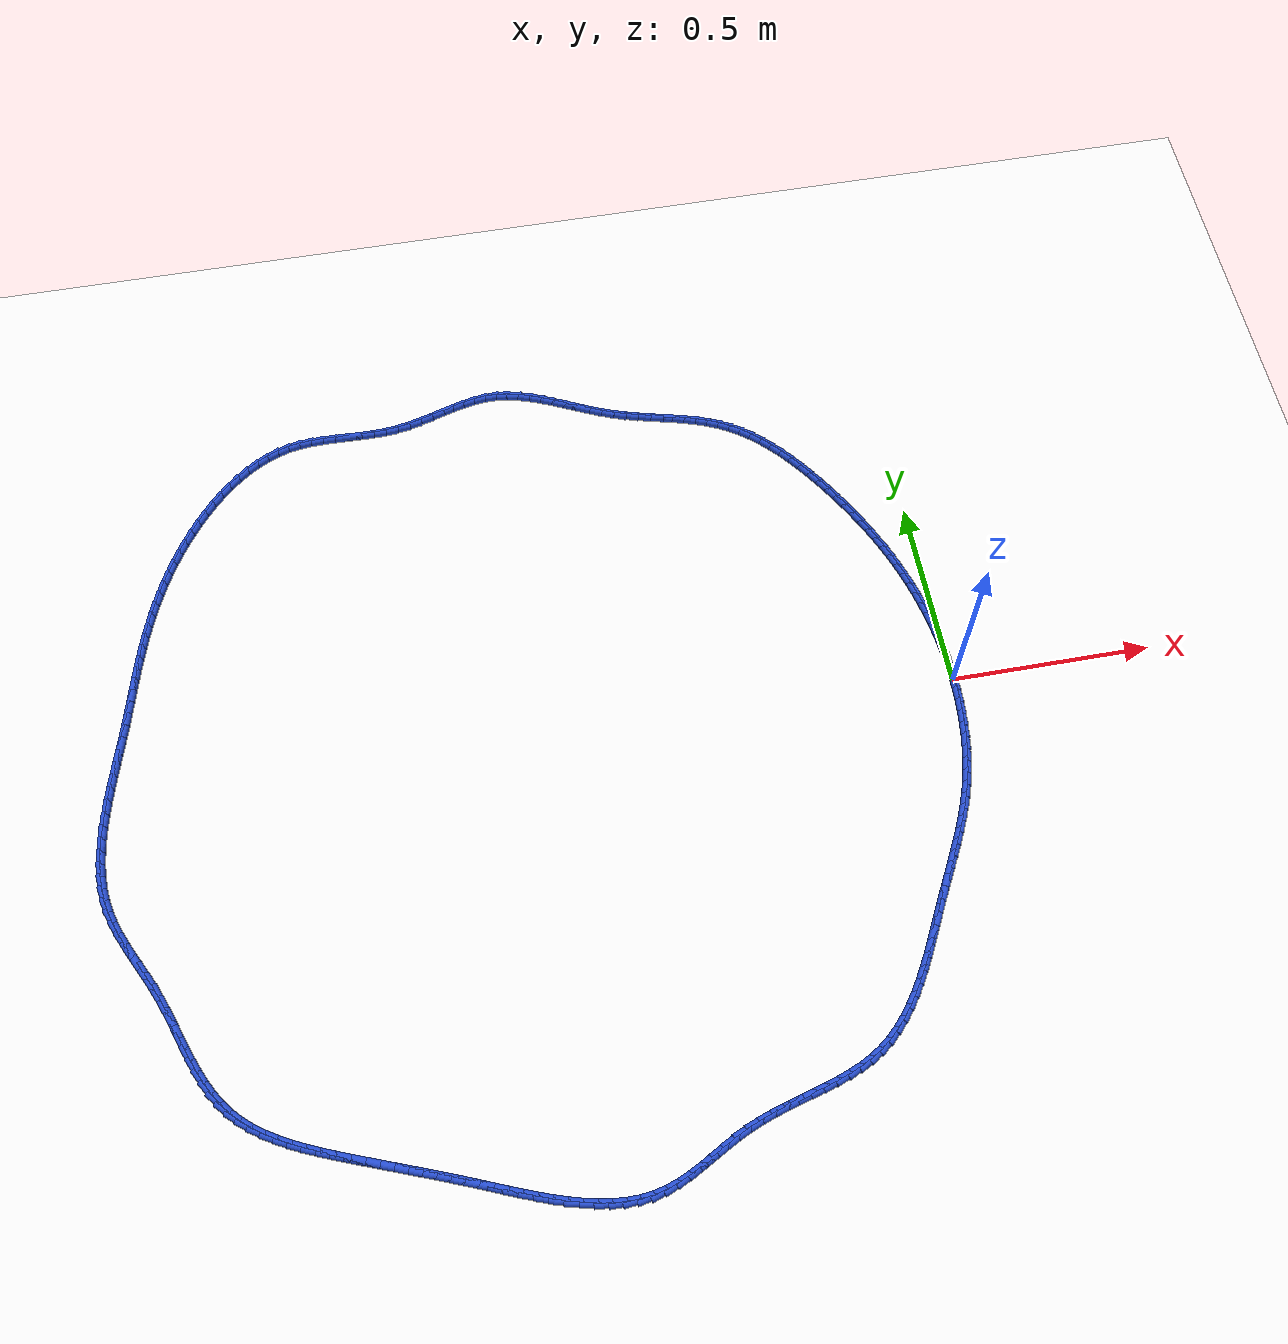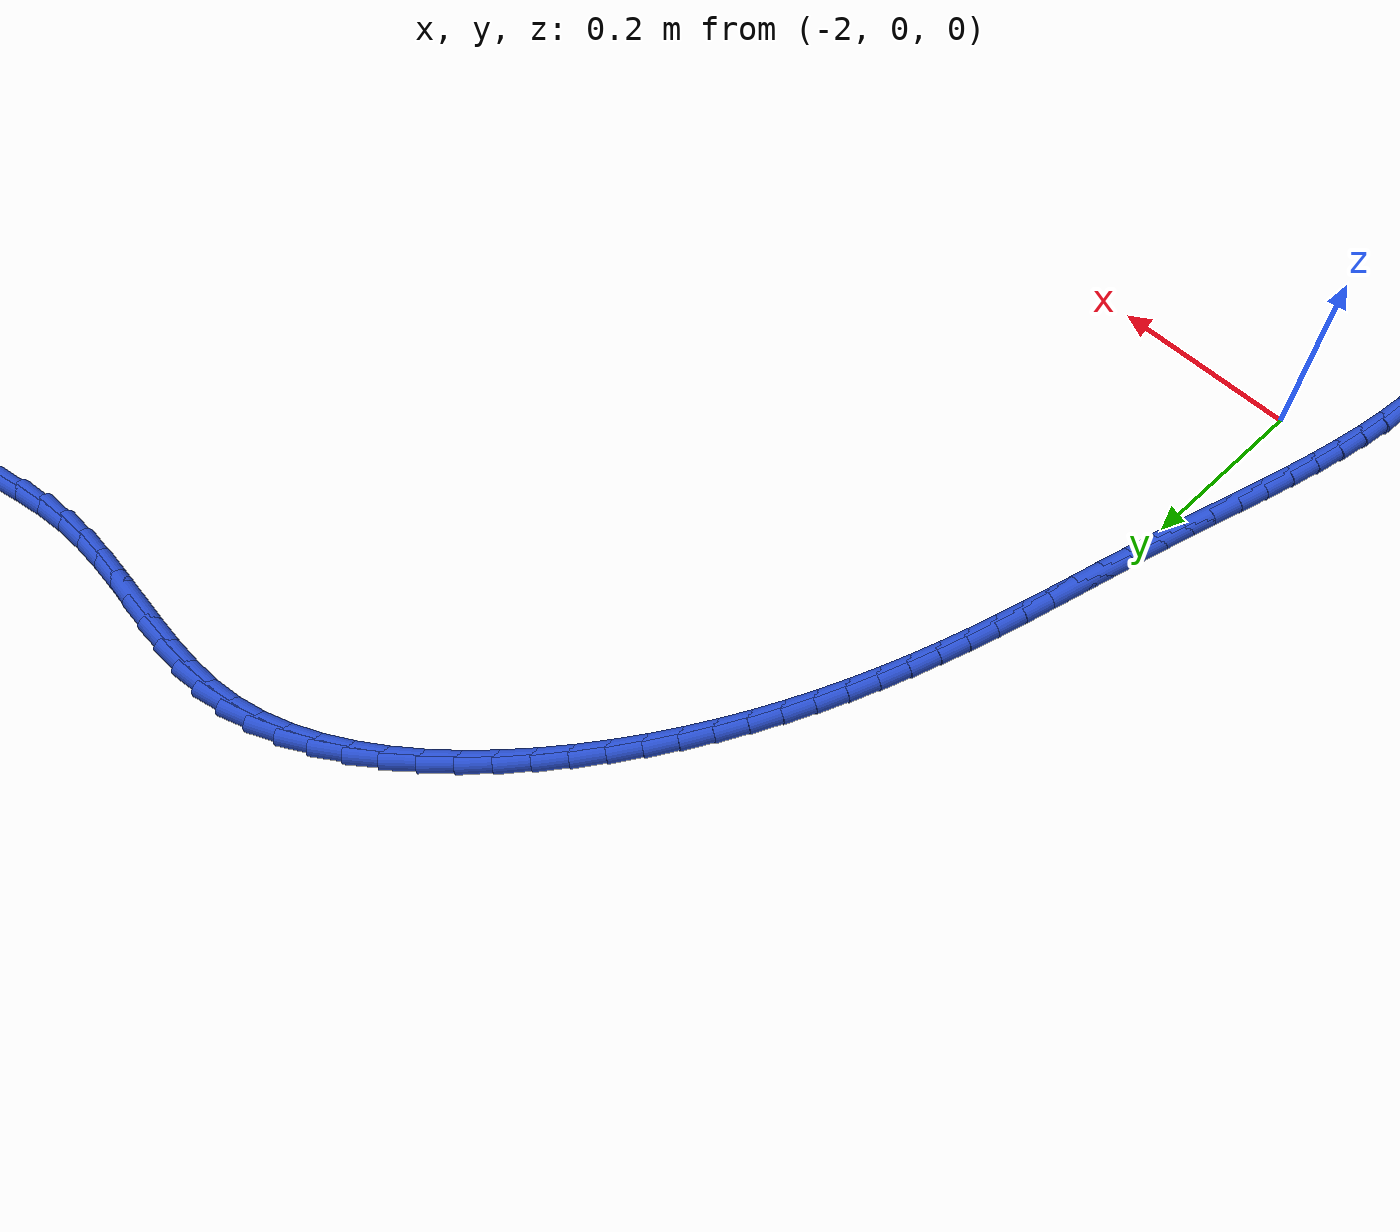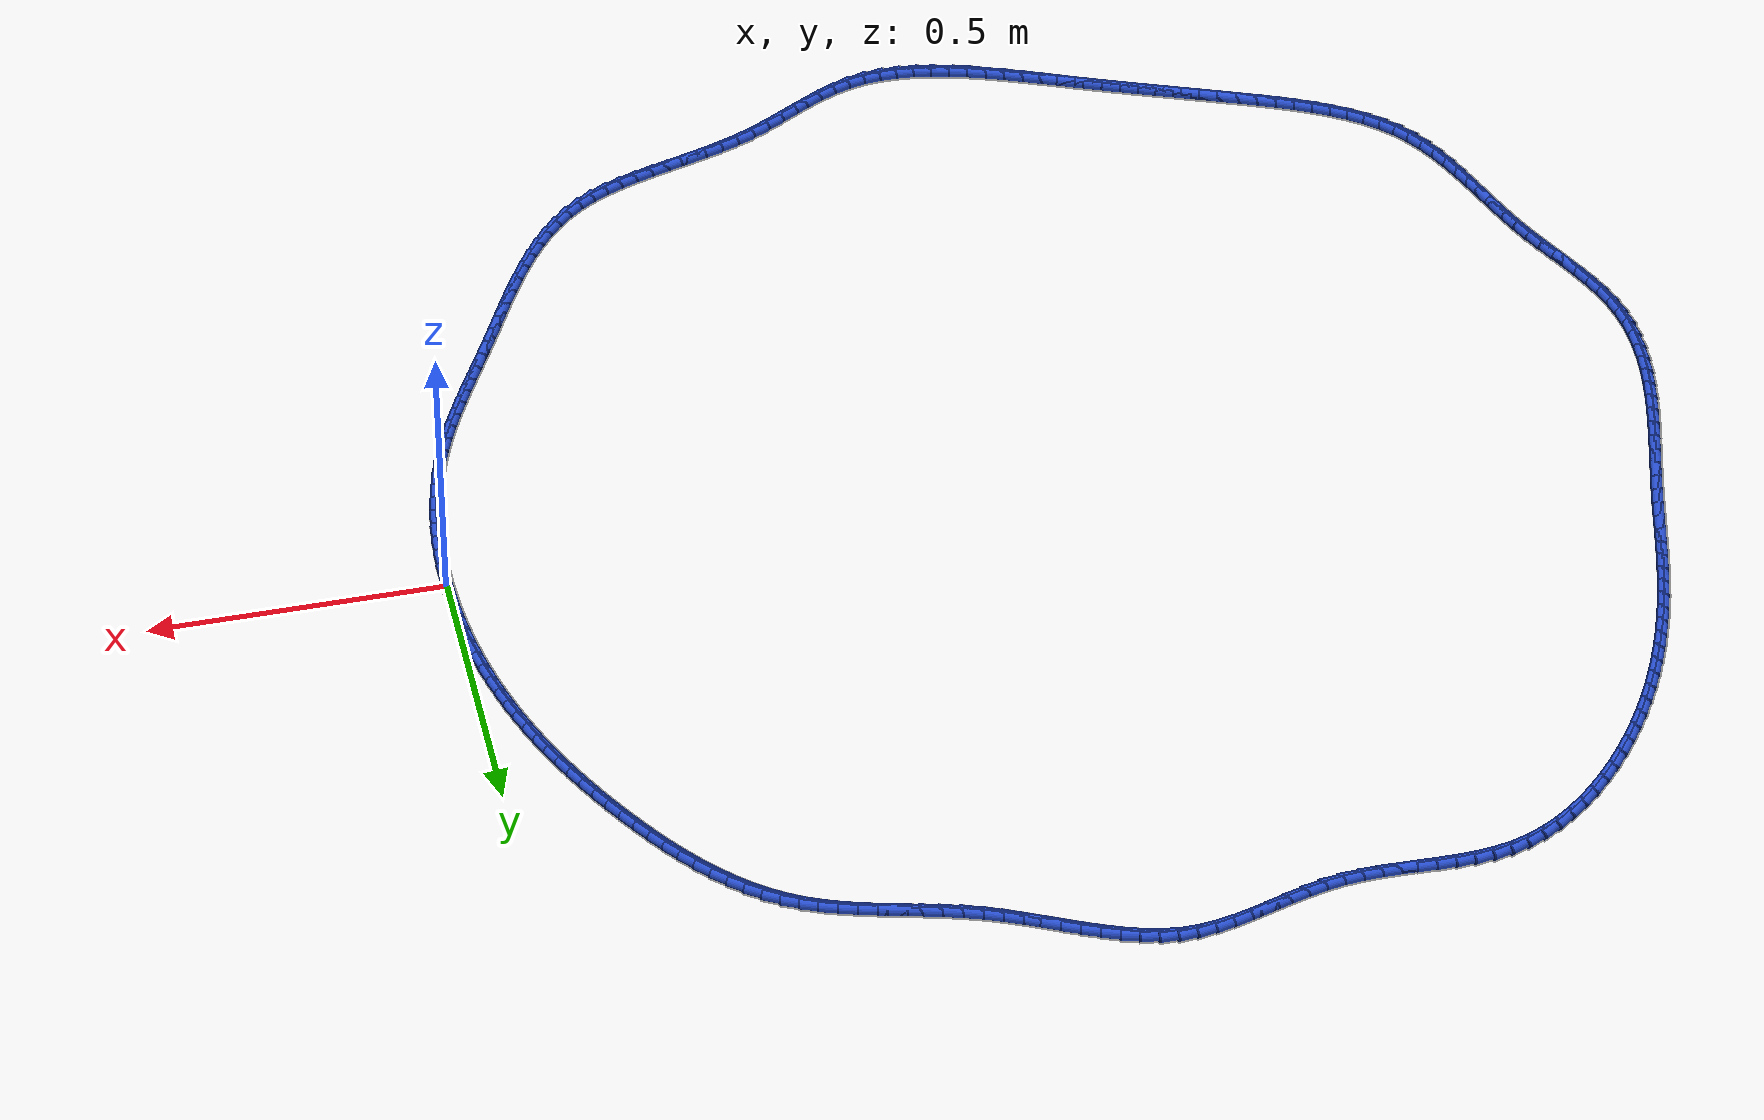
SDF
<sdf version="1.6">
 <world name="default">
  <light name="sun" type="directional">
   <pose>0 0 10 0 -0 0</pose>
   <diffuse>0.8 0.8 0.8 1</diffuse>
   <specular>0.2 0.2 0.2 1</specular>
   <attenuation>
    <range>1000</range>
    <constant>0.9</constant>
    <linear>0.01</linear>
    <quadratic>0.001</quadratic>
   </attenuation>
   <direction>-0.5 0.1 -0.9</direction>
  </light>
  <model name="ground_plane">
   <static>1</static>
   <link name="link">
    <collision name="collision">
     <geometry><plane><normal>0 0 1</normal><size>100 100</size></plane></geometry>
     <surface><friction><ode><mu>100</mu><mu2>50</mu2></ode></friction></surface>
    </collision>
    <visual name="visual">
     <cast_shadows>0</cast_shadows>
     <geometry><plane><normal>0 0 1</normal><size>100 100</size></plane></geometry>
     <material>
      <script><uri>file://media/materials/scripts/gazebo.material</uri><name>Gazebo/WhiteGlow</name></script>
     </material>
    </visual>
   </link>
  </model>
  <gravity>0 0 -9.8</gravity>
  <magnetic_field>6e-06 2.3e-05 -4.2e-05</magnetic_field>
  <atmosphere type="adiabatic"/>
  <physics name="default_physics" default="0" type="ode">
   <max_step_size>0.001</max_step_size>
   <real_time_factor>1</real_time_factor>
   <real_time_update_rate>1000</real_time_update_rate>
  </physics>
  <scene><ambient>0.4 0.4 0.4 1</ambient><background>0.7 0.7 0.7 1</background><shadows>1</shadows></scene>
  <spherical_coordinates>
   <surface_model>EARTH_WGS84</surface_model>
   <latitude_deg>0</latitude_deg>
   <longitude_deg>0</longitude_deg>
   <elevation>0</elevation>
   <heading_deg>0</heading_deg>
  </spherical_coordinates>
  <model name="line">
   <link name="link_0">
    <pose>-8.673617379884035e-19 -3.469446951953614e-17 0.01 0 1.57 -1.546179138487867</pose>
    <collision name="collision">
     <geometry><cylinder><radius>0.01</radius><length>0.08</length></cylinder></geometry>
    </collision>
    <visual name="visual">
     <material>
      <script><name>Gazebo/Blue</name><uri>file://media/materials/scripts/gazebo.material</uri></script>
     </material>
     <geometry><cylinder><radius>0.01</radius><length>0.08</length></cylinder></geometry>
    </visual>
   </link>
   <link name="link_1">
    <pose>-0.0007845097859090664 0.03186193716310851 0.01 0 1.57 -1.515854096692252</pose>
    <collision name="collision">
     <geometry><cylinder><radius>0.01</radius><length>0.08</length></cylinder></geometry>
    </collision>
    <visual name="visual">
     <material>
      <script><name>Gazebo/Blue</name><uri>file://media/materials/scripts/gazebo.material</uri></script>
     </material>
     <geometry><cylinder><radius>0.01</radius><length>0.08</length></cylinder></geometry>
    </visual>
   </link>
   <link name="link_2">
    <pose>-0.002531820838067714 0.06363262652646287 0.01 0 1.57 -1.485835685073196</pose>
    <collision name="collision">
     <geometry><cylinder><radius>0.01</radius><length>0.08</length></cylinder></geometry>
    </collision>
    <visual name="visual">
     <material>
      <script><name>Gazebo/Blue</name><uri>file://media/materials/scripts/gazebo.material</uri></script>
     </material>
     <geometry><cylinder><radius>0.01</radius><length>0.08</length></cylinder></geometry>
    </visual>
   </link>
   <link name="link_3">
    <pose>-0.005227492054490897 0.09528471830067822 0.01 0 1.57 -1.4560993324907086</pose>
    <collision name="collision">
     <geometry><cylinder><radius>0.01</radius><length>0.08</length></cylinder></geometry>
    </collision>
    <visual name="visual">
     <material>
      <script><name>Gazebo/Blue</name><uri>file://media/materials/scripts/gazebo.material</uri></script>
     </material>
     <geometry><cylinder><radius>0.01</radius><length>0.08</length></cylinder></geometry>
    </visual>
   </link>
   <link name="link_4">
    <pose>-0.00885708233319359 0.12679086269636988 0.01 0 1.57 -1.4266184438754645</pose>
    <collision name="collision">
     <geometry><cylinder><radius>0.01</radius><length>0.08</length></cylinder></geometry>
    </collision>
    <visual name="visual">
     <material>
      <script><name>Gazebo/Blue</name><uri>file://media/materials/scripts/gazebo.material</uri></script>
     </material>
     <geometry><cylinder><radius>0.01</radius><length>0.08</length></cylinder></geometry>
    </visual>
   </link>
   <link name="link_5">
    <pose>-0.013406150572190752 0.15812370992415298 0.01 0 1.57 -1.3973646002075648</pose>
    <collision name="collision">
     <geometry><cylinder><radius>0.01</radius><length>0.08</length></cylinder></geometry>
    </collision>
    <visual name="visual">
     <material>
      <script><name>Gazebo/Blue</name><uri>file://media/materials/scripts/gazebo.material</uri></script>
     </material>
     <geometry><cylinder><radius>0.01</radius><length>0.08</length></cylinder></geometry>
    </visual>
   </link>
   <link name="link_6">
    <pose>-0.01886025566949736 0.18925591019464288 0.01 0 1.57 -1.3683077386218947</pose>
    <collision name="collision">
     <geometry><cylinder><radius>0.01</radius><length>0.08</length></cylinder></geometry>
    </collision>
    <visual name="visual">
     <material>
      <script><name>Gazebo/Blue</name><uri>file://media/materials/scripts/gazebo.material</uri></script>
     </material>
     <geometry><cylinder><radius>0.01</radius><length>0.08</length></cylinder></geometry>
    </visual>
   </link>
   <link name="link_7">
    <pose>-0.025204956523128375 0.2201601137184548 0.01 0 1.57 -1.3394163131144312</pose>
    <collision name="collision">
     <geometry><cylinder><radius>0.01</radius><length>0.08</length></cylinder></geometry>
    </collision>
    <visual name="visual">
     <material>
      <script><name>Gazebo/Blue</name><uri>file://media/materials/scripts/gazebo.material</uri></script>
     </material>
     <geometry><cylinder><radius>0.01</radius><length>0.08</length></cylinder></geometry>
    </visual>
   </link>
   <link name="link_8">
    <pose>-0.03242581203109877 0.2508089707062039 0.01 0 1.57 -1.310657436919345</pose>
    <collision name="collision">
     <geometry><cylinder><radius>0.01</radius><length>0.08</length></cylinder></geometry>
    </collision>
    <visual name="visual">
     <material>
      <script><name>Gazebo/Blue</name><uri>file://media/materials/scripts/gazebo.material</uri></script>
     </material>
     <geometry><cylinder><radius>0.01</radius><length>0.08</length></cylinder></geometry>
    </visual>
   </link>
   <link name="link_9">
    <pose>-0.040508381091423476 0.28117513136850547 0.01 0 1.57 -1.2820068108407752</pose>
    <collision name="collision">
     <geometry><cylinder><radius>0.01</radius><length>0.08</length></cylinder></geometry>
    </collision>
    <visual name="visual">
     <material>
      <script><name>Gazebo/Blue</name><uri>file://media/materials/scripts/gazebo.material</uri></script>
     </material>
     <geometry><cylinder><radius>0.01</radius><length>0.08</length></cylinder></geometry>
    </visual>
   </link>
   <link name="link_10">
    <pose>-0.04943826534335735 0.31123246902436735 0.01 0 1.57 -1.2536332291583911</pose>
    <collision name="collision">
     <geometry><cylinder><radius>0.01</radius><length>0.08</length></cylinder></geometry>
    </collision>
    <visual name="visual">
     <material>
      <script><name>Gazebo/Blue</name><uri>file://media/materials/scripts/gazebo.material</uri></script>
     </material>
     <geometry><cylinder><radius>0.01</radius><length>0.08</length></cylinder></geometry>
    </visual>
   </link>
   <link name="link_11">
    <pose>-0.05920185377134122 0.3409773881245305 0.01 0 1.57 -1.2257566993301436</pose>
    <collision name="collision">
     <geometry><cylinder><radius>0.01</radius><length>0.08</length></cylinder></geometry>
    </collision>
    <visual name="visual">
     <material>
      <script><name>Gazebo/Blue</name><uri>file://media/materials/scripts/gazebo.material</uri></script>
     </material>
     <geometry><cylinder><radius>0.01</radius><length>0.08</length></cylinder></geometry>
    </visual>
   </link>
   <link name="link_12">
    <pose>-0.06978622724726852 0.3704260925769683 0.01 0 1.57 -1.1984580024994478</pose>
    <collision name="collision">
     <geometry><cylinder><radius>0.01</radius><length>0.08</length></cylinder></geometry>
    </collision>
    <visual name="visual">
     <material>
      <script><name>Gazebo/Blue</name><uri>file://media/materials/scripts/gazebo.material</uri></script>
     </material>
     <geometry><cylinder><radius>0.01</radius><length>0.08</length></cylinder></geometry>
    </visual>
   </link>
   <link name="link_13">
    <pose>-0.08117849019270099 0.39959546020077574 0.01 0 1.57 -1.171805971372981</pose>
    <collision name="collision">
     <geometry><cylinder><radius>0.01</radius><length>0.08</length></cylinder></geometry>
    </collision>
    <visual name="visual">
     <material>
      <script><name>Gazebo/Blue</name><uri>file://media/materials/scripts/gazebo.material</uri></script>
     </material>
     <geometry><cylinder><radius>0.01</radius><length>0.08</length></cylinder></geometry>
    </visual>
   </link>
   <link name="link_14">
    <pose>-0.09336574702920032 0.4285023688150477 0.01 0 1.57 -1.1458623187010317</pose>
    <collision name="collision">
     <geometry><cylinder><radius>0.01</radius><length>0.08</length></cylinder></geometry>
    </collision>
    <visual name="visual">
     <material>
      <script><name>Gazebo/Blue</name><uri>file://media/materials/scripts/gazebo.material</uri></script>
     </material>
     <geometry><cylinder><radius>0.01</radius><length>0.08</length></cylinder></geometry>
    </visual>
   </link>
   <link name="link_15">
    <pose>-0.10633510217832819 0.4571636962388792 0.01 0 1.57 -1.1206812737849448</pose>
    <collision name="collision">
     <geometry><cylinder><radius>0.01</radius><length>0.08</length></cylinder></geometry>
    </collision>
    <visual name="visual">
     <material>
      <script><name>Gazebo/Blue</name><uri>file://media/materials/scripts/gazebo.material</uri></script>
     </material>
     <geometry><cylinder><radius>0.01</radius><length>0.08</length></cylinder></geometry>
    </visual>
   </link>
   <link name="link_16">
    <pose>-0.12007366006164631 0.4855963202913651 0.01 0 1.57 -1.096309419617392</pose>
    <collision name="collision">
     <geometry><cylinder><radius>0.01</radius><length>0.08</length></cylinder></geometry>
    </collision>
    <visual name="visual">
     <material>
      <script><name>Gazebo/Blue</name><uri>file://media/materials/scripts/gazebo.material</uri></script>
     </material>
     <geometry><cylinder><radius>0.01</radius><length>0.08</length></cylinder></geometry>
    </visual>
   </link>
   <link name="link_17">
    <pose>-0.1345685251007164 0.5138171187916004 0.01 0 1.57 -1.0727857141332735</pose>
    <collision name="collision">
     <geometry><cylinder><radius>0.01</radius><length>0.08</length></cylinder></geometry>
    </collision>
    <visual name="visual">
     <material>
      <script><name>Gazebo/Blue</name><uri>file://media/materials/scripts/gazebo.material</uri></script>
     </material>
     <geometry><cylinder><radius>0.01</radius><length>0.08</length></cylinder></geometry>
    </visual>
   </link>
   <link name="link_18">
    <pose>-0.14980680171710006 0.5418429695586797 0.01 0 1.57 -1.050141672897541</pose>
    <collision name="collision">
     <geometry><cylinder><radius>0.01</radius><length>0.08</length></cylinder></geometry>
    </collision>
    <visual name="visual">
     <material>
      <script><name>Gazebo/Blue</name><uri>file://media/materials/scripts/gazebo.material</uri></script>
     </material>
     <geometry><cylinder><radius>0.01</radius><length>0.08</length></cylinder></geometry>
    </visual>
   </link>
   <link name="link_19">
    <pose>-0.16577559433235917 0.5696907504116987 0.01 0 1.57 -1.0284016866831533</pose>
    <collision name="collision">
     <geometry><cylinder><radius>0.01</radius><length>0.08</length></cylinder></geometry>
    </collision>
    <visual name="visual">
     <material>
      <script><name>Gazebo/Blue</name><uri>file://media/materials/scripts/gazebo.material</uri></script>
     </material>
     <geometry><cylinder><radius>0.01</radius><length>0.08</length></cylinder></geometry>
    </visual>
   </link>
   <link name="link_20">
    <pose>-0.18246200736805523 0.5973773391697513 0.01 0 1.57 -1.0071248750660453</pose>
    <collision name="collision">
     <geometry><cylinder><radius>0.01</radius><length>0.08</length></cylinder></geometry>
    </collision>
    <visual name="visual">
     <material>
      <script><name>Gazebo/Blue</name><uri>file://media/materials/scripts/gazebo.material</uri></script>
     </material>
     <geometry><cylinder><radius>0.01</radius><length>0.08</length></cylinder></geometry>
    </visual>
   </link>
   <link name="link_21">
    <pose>-0.19985814635557805 0.624899568883812 0.01 0 1.57 -0.9828931528680305</pose>
    <collision name="collision">
     <geometry><cylinder><radius>0.01</radius><length>0.08</length></cylinder></geometry>
    </collision>
    <visual name="visual">
     <material>
      <script><name>Gazebo/Blue</name><uri>file://media/materials/scripts/gazebo.material</uri></script>
     </material>
     <geometry><cylinder><radius>0.01</radius><length>0.08</length></cylinder></geometry>
    </visual>
   </link>
   <link name="link_22">
    <pose>-0.21799276981472274 0.6521073650825647 0.01 0 1.57 -0.9539676432649176</pose>
    <collision name="collision">
     <geometry><cylinder><radius>0.01</radius><length>0.08</length></cylinder></geometry>
    </collision>
    <visual name="visual">
     <material>
      <script><name>Gazebo/Blue</name><uri>file://media/materials/scripts/gazebo.material</uri></script>
     </material>
     <geometry><cylinder><radius>0.01</radius><length>0.08</length></cylinder></geometry>
    </visual>
   </link>
   <link name="link_23">
    <pose>-0.23691094436011548 0.6787852894073502 0.01 0 1.57 -0.9199902012766192</pose>
    <collision name="collision">
     <geometry><cylinder><radius>0.01</radius><length>0.08</length></cylinder></geometry>
    </collision>
    <visual name="visual">
     <material>
      <script><name>Gazebo/Blue</name><uri>file://media/materials/scripts/gazebo.material</uri></script>
     </material>
     <geometry><cylinder><radius>0.01</radius><length>0.08</length></cylinder></geometry>
    </visual>
   </link>
   <link name="link_24">
    <pose>-0.2566578109968819 0.7047176053376286 0.01 0 1.57 -0.8805282683018618</pose>
    <collision name="collision">
     <geometry><cylinder><radius>0.01</radius><length>0.08</length></cylinder></geometry>
    </collision>
    <visual name="visual">
     <material>
      <script><name>Gazebo/Blue</name><uri>file://media/materials/scripts/gazebo.material</uri></script>
     </material>
     <geometry><cylinder><radius>0.01</radius><length>0.08</length></cylinder></geometry>
    </visual>
   </link>
   <link name="link_25">
    <pose>-0.27727851073014775 0.7296885763528607 0.01 0 1.57 -0.8350823358551457</pose>
    <collision name="collision">
     <geometry><cylinder><radius>0.01</radius><length>0.08</length></cylinder></geometry>
    </collision>
    <visual name="visual">
     <material>
      <script><name>Gazebo/Blue</name><uri>file://media/materials/scripts/gazebo.material</uri></script>
     </material>
     <geometry><cylinder><radius>0.01</radius><length>0.08</length></cylinder></geometry>
    </visual>
   </link>
   <link name="link_26">
    <pose>-0.2988181845650385 0.7534824659325065 0.01 0 1.57 -0.7831107241831605</pose>
    <collision name="collision">
     <geometry><cylinder><radius>0.01</radius><length>0.08</length></cylinder></geometry>
    </collision>
    <visual name="visual">
     <material>
      <script><name>Gazebo/Blue</name><uri>file://media/materials/scripts/gazebo.material</uri></script>
     </material>
     <geometry><cylinder><radius>0.01</radius><length>0.08</length></cylinder></geometry>
    </visual>
   </link>
   <link name="link_27">
    <pose>-0.32132197350667996 0.775883537556027 0.01 0 1.57 -0.724071406500299</pose>
    <collision name="collision">
     <geometry><cylinder><radius>0.01</radius><length>0.08</length></cylinder></geometry>
    </collision>
    <visual name="visual">
     <material>
      <script><name>Gazebo/Blue</name><uri>file://media/materials/scripts/gazebo.material</uri></script>
     </material>
     <geometry><cylinder><radius>0.01</radius><length>0.08</length></cylinder></geometry>
    </visual>
   </link>
   <link name="link_28">
    <pose>-0.3448350185601977 0.7966760547028827 0.01 0 1.57 -0.6574881831857523</pose>
    <collision name="collision">
     <geometry><cylinder><radius>0.01</radius><length>0.08</length></cylinder></geometry>
    </collision>
    <visual name="visual">
     <material>
      <script><name>Gazebo/Blue</name><uri>file://media/materials/scripts/gazebo.material</uri></script>
     </material>
     <geometry><cylinder><radius>0.01</radius><length>0.08</length></cylinder></geometry>
    </visual>
   </link>
   <link name="link_29">
    <pose>-0.3694024607307172 0.8156442808525334 0.01 0 1.57 -0.5830470435300353</pose>
    <collision name="collision">
     <geometry><cylinder><radius>0.01</radius><length>0.08</length></cylinder></geometry>
    </collision>
    <visual name="visual">
     <material>
      <script><name>Gazebo/Blue</name><uri>file://media/materials/scripts/gazebo.material</uri></script>
     </material>
     <geometry><cylinder><radius>0.01</radius><length>0.08</length></cylinder></geometry>
    </visual>
   </link>
   <link name="link_30">
    <pose>-0.3950694410233643 0.83257247948444 0.01 0 1.57 -0.5008786834999343</pose>
    <collision name="collision">
     <geometry><cylinder><radius>0.01</radius><length>0.08</length></cylinder></geometry>
    </collision>
    <visual name="visual">
     <material>
      <script><name>Gazebo/Blue</name><uri>file://media/materials/scripts/gazebo.material</uri></script>
     </material>
     <geometry><cylinder><radius>0.01</radius><length>0.08</length></cylinder></geometry>
    </visual>
   </link>
   <link name="link_31">
    <pose>-0.4218796081622203 0.8472495435917111 0.01 0 1.57 -0.4199276455290666</pose>
    <collision name="collision">
     <geometry><cylinder><radius>0.01</radius><length>0.08</length></cylinder></geometry>
    </collision>
    <visual name="visual">
     <material>
      <script><name>Gazebo/Blue</name><uri>file://media/materials/scripts/gazebo.material</uri></script>
     </material>
     <geometry><cylinder><radius>0.01</radius><length>0.08</length></cylinder></geometry>
    </visual>
   </link>
   <link name="link_32">
    <pose>-0.4497961777112475 0.8597138945079991 0.01 0 1.57 -0.3537949848907438</pose>
    <collision name="collision">
     <geometry><cylinder><radius>0.01</radius><length>0.08</length></cylinder></geometry>
    </collision>
    <visual name="visual">
     <material>
      <script><name>Gazebo/Blue</name><uri>file://media/materials/scripts/gazebo.material</uri></script>
     </material>
     <geometry><cylinder><radius>0.01</radius><length>0.08</length></cylinder></geometry>
    </visual>
   </link>
   <link name="link_33">
    <pose>-0.4786626644284542 0.8703753021926585 0.01 0 1.57 -0.3038911339191584</pose>
    <collision name="collision">
     <geometry><cylinder><radius>0.01</radius><length>0.08</length></cylinder></geometry>
    </collision>
    <visual name="visual">
     <material>
      <script><name>Gazebo/Blue</name><uri>file://media/materials/scripts/gazebo.material</uri></script>
     </material>
     <geometry><cylinder><radius>0.01</radius><length>0.08</length></cylinder></geometry>
    </visual>
   </link>
   <link name="link_34">
    <pose>-0.5083128460349068 0.8796737438810759 0.01 0 1.57 -0.26995806032222636</pose>
    <collision name="collision">
     <geometry><cylinder><radius>0.01</radius><length>0.08</length></cylinder></geometry>
    </collision>
    <visual name="visual">
     <material>
      <script><name>Gazebo/Blue</name><uri>file://media/materials/scripts/gazebo.material</uri></script>
     </material>
     <geometry><cylinder><radius>0.01</radius><length>0.08</length></cylinder></geometry>
    </visual>
   </link>
   <link name="link_35">
    <pose>-0.5385805002516725 0.8880491968086387 0.01 0 1.57 -0.2514852141585984</pose>
    <collision name="collision">
     <geometry><cylinder><radius>0.01</radius><length>0.08</length></cylinder></geometry>
    </collision>
    <visual name="visual">
     <material>
      <script><name>Gazebo/Blue</name><uri>file://media/materials/scripts/gazebo.material</uri></script>
     </material>
     <geometry><cylinder><radius>0.01</radius><length>0.08</length></cylinder></geometry>
    </visual>
   </link>
   <link name="link_36">
    <pose>-0.5692994047998174 0.8959416382107334 0.01 0 1.57 -0.24796424889364851</pose>
    <collision name="collision">
     <geometry><cylinder><radius>0.01</radius><length>0.08</length></cylinder></geometry>
    </collision>
    <visual name="visual">
     <material>
      <script><name>Gazebo/Blue</name><uri>file://media/materials/scripts/gazebo.material</uri></script>
     </material>
     <geometry><cylinder><radius>0.01</radius><length>0.08</length></cylinder></geometry>
    </visual>
   </link>
   <link name="link_37">
    <pose>-0.6003033374004086 0.9037910453227471 0.01 0 1.57 -0.2590104353326691</pose>
    <collision name="collision">
     <geometry><cylinder><radius>0.01</radius><length>0.08</length></cylinder></geometry>
    </collision>
    <visual name="visual">
     <material>
      <script><name>Gazebo/Blue</name><uri>file://media/materials/scripts/gazebo.material</uri></script>
     </material>
     <geometry><cylinder><radius>0.01</radius><length>0.08</length></cylinder></geometry>
    </visual>
   </link>
   <link name="link_38">
    <pose>-0.6314260757745126 0.9120373953800663 0.01 0 1.57 -0.28437631583223855</pose>
    <collision name="collision">
     <geometry><cylinder><radius>0.01</radius><length>0.08</length></cylinder></geometry>
    </collision>
    <visual name="visual">
     <material>
      <script><name>Gazebo/Blue</name><uri>file://media/materials/scripts/gazebo.material</uri></script>
     </material>
     <geometry><cylinder><radius>0.01</radius><length>0.08</length></cylinder></geometry>
    </visual>
   </link>
   <link name="link_39">
    <pose>-0.6625013976431957 0.9211206656180785 0.01 0 1.57 -0.3238761465801971</pose>
    <collision name="collision">
     <geometry><cylinder><radius>0.01</radius><length>0.08</length></cylinder></geometry>
    </collision>
    <visual name="visual">
     <material>
      <script><name>Gazebo/Blue</name><uri>file://media/materials/scripts/gazebo.material</uri></script>
     </material>
     <geometry><cylinder><radius>0.01</radius><length>0.08</length></cylinder></geometry>
    </visual>
   </link>
   <link name="link_40">
    <pose>-0.6933630807275251 0.93148083327217 0.01 0 1.57 -0.3736610651016851</pose>
    <collision name="collision">
     <geometry><cylinder><radius>0.01</radius><length>0.08</length></cylinder></geometry>
    </collision>
    <visual name="visual">
     <material>
      <script><name>Gazebo/Blue</name><uri>file://media/materials/scripts/gazebo.material</uri></script>
     </material>
     <geometry><cylinder><radius>0.01</radius><length>0.08</length></cylinder></geometry>
    </visual>
   </link>
   <link name="link_41">
    <pose>-0.7238711940789038 0.9434424847896838 0.01 0 1.57 -0.4135131069568589</pose>
    <collision name="collision">
     <geometry><cylinder><radius>0.01</radius><length>0.08</length></cylinder></geometry>
    </collision>
    <visual name="visual">
     <material>
      <script><name>Gazebo/Blue</name><uri>file://media/materials/scripts/gazebo.material</uri></script>
     </material>
     <geometry><cylinder><radius>0.01</radius><length>0.08</length></cylinder></geometry>
    </visual>
   </link>
   <link name="link_42">
    <pose>-0.7540342982452174 0.9566784879495669 0.01 0 1.57 -0.43693600392346466</pose>
    <collision name="collision">
     <geometry><cylinder><radius>0.01</radius><length>0.08</length></cylinder></geometry>
    </collision>
    <visual name="visual">
     <material>
      <script><name>Gazebo/Blue</name><uri>file://media/materials/scripts/gazebo.material</uri></script>
     </material>
     <geometry><cylinder><radius>0.01</radius><length>0.08</length></cylinder></geometry>
    </visual>
   </link>
   <link name="link_43">
    <pose>-0.7839130333864973 0.9706331367990634 0.01 0 1.57 -0.44430604719258404</pose>
    <collision name="collision">
     <geometry><cylinder><radius>0.01</radius><length>0.08</length></cylinder></geometry>
    </collision>
    <visual name="visual">
     <material>
      <script><name>Gazebo/Blue</name><uri>file://media/materials/scripts/gazebo.material</uri></script>
     </material>
     <geometry><cylinder><radius>0.01</radius><length>0.08</length></cylinder></geometry>
    </visual>
   </link>
   <link name="link_44">
    <pose>-0.8135680959028473 0.984750478551717 0.01 0 1.57 -0.4355437241821871</pose>
    <collision name="collision">
     <geometry><cylinder><radius>0.01</radius><length>0.08</length></cylinder></geometry>
    </collision>
    <visual name="visual">
     <material>
      <script><name>Gazebo/Blue</name><uri>file://media/materials/scripts/gazebo.material</uri></script>
     </material>
     <geometry><cylinder><radius>0.01</radius><length>0.08</length></cylinder></geometry>
    </visual>
   </link>
   <link name="link_45">
    <pose>-0.8430601821943711 0.9984745604210705 0.01 0 1.57 -0.4100326886450885</pose>
    <collision name="collision">
     <geometry><cylinder><radius>0.01</radius><length>0.08</length></cylinder></geometry>
    </collision>
    <visual name="visual">
     <material>
      <script><name>Gazebo/Blue</name><uri>file://media/materials/scripts/gazebo.material</uri></script>
     </material>
     <geometry><cylinder><radius>0.01</radius><length>0.08</length></cylinder></geometry>
    </visual>
   </link>
   <link name="link_46">
    <pose>-0.8724499886611731 1.011249429620668 0.01 0 1.57 -0.36663722793771414</pose>
    <collision name="collision">
     <geometry><cylinder><radius>0.01</radius><length>0.08</length></cylinder></geometry>
    </collision>
    <visual name="visual">
     <material>
      <script><name>Gazebo/Blue</name><uri>file://media/materials/scripts/gazebo.material</uri></script>
     </material>
     <geometry><cylinder><radius>0.01</radius><length>0.08</length></cylinder></geometry>
    </visual>
   </link>
   <link name="link_47">
    <pose>-0.901798211703357 1.0225191333640524 0.01 0 1.57 -0.3038553433925795</pose>
    <collision name="collision">
     <geometry><cylinder><radius>0.01</radius><length>0.08</length></cylinder></geometry>
    </collision>
    <visual name="visual">
     <material>
      <script><name>Gazebo/Blue</name><uri>file://media/materials/scripts/gazebo.material</uri></script>
     </material>
     <geometry><cylinder><radius>0.01</radius><length>0.08</length></cylinder></geometry>
    </visual>
   </link>
   <link name="link_48">
    <pose>-0.9311655477210272 1.0317277188647673 0.01 0 1.57 -0.22021218021429617</pose>
    <collision name="collision">
     <geometry><cylinder><radius>0.01</radius><length>0.08</length></cylinder></geometry>
    </collision>
    <visual name="visual">
     <material>
      <script><name>Gazebo/Blue</name><uri>file://media/materials/scripts/gazebo.material</uri></script>
     </material>
     <geometry><cylinder><radius>0.01</radius><length>0.08</length></cylinder></geometry>
    </visual>
   </link>
   <link name="link_49">
    <pose>-0.9606126931142873 1.0383192333363558 0.01 0 1.57 -0.11502772581393149</pose>
    <collision name="collision">
     <geometry><cylinder><radius>0.01</radius><length>0.08</length></cylinder></geometry>
    </collision>
    <visual name="visual">
     <material>
      <script><name>Gazebo/Blue</name><uri>file://media/materials/scripts/gazebo.material</uri></script>
     </material>
     <geometry><cylinder><radius>0.01</radius><length>0.08</length></cylinder></geometry>
    </visual>
   </link>
   <link name="link_50">
    <pose>-0.9902003442832412 1.0417377239923613 0.01 0 1.57 0.00824155825658132</pose>
    <collision name="collision">
     <geometry><cylinder><radius>0.01</radius><length>0.08</length></cylinder></geometry>
    </collision>
    <visual name="visual">
     <material>
      <script><name>Gazebo/Blue</name><uri>file://media/materials/scripts/gazebo.material</uri></script>
     </material>
     <geometry><cylinder><radius>0.01</radius><length>0.08</length></cylinder></geometry>
    </visual>
   </link>
   <link name="link_51">
    <pose>-1.0199865515981614 1.0414922336713381 0.01 0 1.57 0.12058958994074306</pose>
    <collision name="collision">
     <geometry><cylinder><radius>0.01</radius><length>0.08</length></cylinder></geometry>
    </collision>
    <visual name="visual">
     <material>
      <script><name>Gazebo/Blue</name><uri>file://media/materials/scripts/gazebo.material</uri></script>
     </material>
     <geometry><cylinder><radius>0.01</radius><length>0.08</length></cylinder></geometry>
    </visual>
   </link>
   <link name="link_52">
    <pose>-1.0499982752725525 1.0378554867647123 0.01 0 1.57 0.20406008757709</pose>
    <collision name="collision">
     <geometry><cylinder><radius>0.01</radius><length>0.08</length></cylinder></geometry>
    </collision>
    <visual name="visual">
     <material>
      <script><name>Gazebo/Blue</name><uri>file://media/materials/scripts/gazebo.material</uri></script>
     </material>
     <geometry><cylinder><radius>0.01</radius><length>0.08</length></cylinder></geometry>
    </visual>
   </link>
   <link name="link_53">
    <pose>-1.0802422595084933 1.0315967826768655 0.01 0 1.57 0.2598121670030946</pose>
    <collision name="collision">
     <geometry><cylinder><radius>0.01</radius><length>0.08</length></cylinder></geometry>
    </collision>
    <visual name="visual">
     <material>
      <script><name>Gazebo/Blue</name><uri>file://media/materials/scripts/gazebo.material</uri></script>
     </material>
     <geometry><cylinder><radius>0.01</radius><length>0.08</length></cylinder></geometry>
    </visual>
   </link>
   <link name="link_54">
    <pose>-1.1107249044114034 1.0234938730136556 0.01 0 1.57 0.28999472140376986</pose>
    <collision name="collision">
     <geometry><cylinder><radius>0.01</radius><length>0.08</length></cylinder></geometry>
    </collision>
    <visual name="visual">
     <material>
      <script><name>Gazebo/Blue</name><uri>file://media/materials/scripts/gazebo.material</uri></script>
     </material>
     <geometry><cylinder><radius>0.01</radius><length>0.08</length></cylinder></geometry>
    </visual>
   </link>
   <link name="link_55">
    <pose>-1.141452610086704 1.0143245093809423 0.01 0 1.57 0.2963157928271445</pose>
    <collision name="collision">
     <geometry><cylinder><radius>0.01</radius><length>0.08</length></cylinder></geometry>
    </collision>
    <visual name="visual">
     <material>
      <script><name>Gazebo/Blue</name><uri>file://media/materials/scripts/gazebo.material</uri></script>
     </material>
     <geometry><cylinder><radius>0.01</radius><length>0.08</length></cylinder></geometry>
    </visual>
   </link>
   <link name="link_56">
    <pose>-1.172431776639817 1.004866443384584 0.01 0 1.57 0.2796059381843281</pose>
    <collision name="collision">
     <geometry><cylinder><radius>0.01</radius><length>0.08</length></cylinder></geometry>
    </collision>
    <visual name="visual">
     <material>
      <script><name>Gazebo/Blue</name><uri>file://media/materials/scripts/gazebo.material</uri></script>
     </material>
     <geometry><cylinder><radius>0.01</radius><length>0.08</length></cylinder></geometry>
    </visual>
   </link>
   <link name="link_57">
    <pose>-1.2036688041761627 0.9958974266304397 0.01 0 1.57 0.23980004949641215</pose>
    <collision name="collision">
     <geometry><cylinder><radius>0.01</radius><length>0.08</length></cylinder></geometry>
    </collision>
    <visual name="visual">
     <material>
      <script><name>Gazebo/Blue</name><uri>file://media/materials/scripts/gazebo.material</uri></script>
     </material>
     <geometry><cylinder><radius>0.01</radius><length>0.08</length></cylinder></geometry>
    </visual>
   </link>
   <link name="link_58">
    <pose>-1.2351700928011624 0.9881952107243684 0.01 0 1.57 0.17622768772882644</pose>
    <collision name="collision">
     <geometry><cylinder><radius>0.01</radius><length>0.08</length></cylinder></geometry>
    </collision>
    <visual name="visual">
     <material>
      <script><name>Gazebo/Blue</name><uri>file://media/materials/scripts/gazebo.material</uri></script>
     </material>
     <geometry><cylinder><radius>0.01</radius><length>0.08</length></cylinder></geometry>
    </visual>
   </link>
   <link name="link_59">
    <pose>-1.2669420320097329 0.9825374239374634 0.01 0 1.57 0.09775474044704364</pose>
    <collision name="collision">
     <geometry><cylinder><radius>0.01</radius><length>0.08</length></cylinder></geometry>
    </collision>
    <visual name="visual">
     <material>
      <script><name>Gazebo/Blue</name><uri>file://media/materials/scripts/gazebo.material</uri></script>
     </material>
     <geometry><cylinder><radius>0.01</radius><length>0.08</length></cylinder></geometry>
    </visual>
   </link>
   <link name="link_60">
    <pose>-1.298964801561053 0.9793970368646946 0.01 0 1.57 0.03450498983983951</pose>
    <collision name="collision">
     <geometry><cylinder><radius>0.01</radius><length>0.08</length></cylinder></geometry>
    </collision>
    <visual name="visual">
     <material>
      <script><name>Gazebo/Blue</name><uri>file://media/materials/scripts/gazebo.material</uri></script>
     </material>
     <geometry><cylinder><radius>0.01</radius><length>0.08</length></cylinder></geometry>
    </visual>
   </link>
   <link name="link_61">
    <pose>-1.3311359502196987 0.9782865309514278 0.01 0 1.57 -0.007547643432789391</pose>
    <collision name="collision">
     <geometry><cylinder><radius>0.01</radius><length>0.08</length></cylinder></geometry>
    </collision>
    <visual name="visual">
     <material>
      <script><name>Gazebo/Blue</name><uri>file://media/materials/scripts/gazebo.material</uri></script>
     </material>
     <geometry><cylinder><radius>0.01</radius><length>0.08</length></cylinder></geometry>
    </visual>
   </link>
   <link name="link_62">
    <pose>-1.3633367832600192 0.978529575972648 0.01 0 1.57 -0.02865031762360676</pose>
    <collision name="collision">
     <geometry><cylinder><radius>0.01</radius><length>0.08</length></cylinder></geometry>
    </collision>
    <visual name="visual">
     <material>
      <script><name>Gazebo/Blue</name><uri>file://media/materials/scripts/gazebo.material</uri></script>
     </material>
     <geometry><cylinder><radius>0.01</radius><length>0.08</length></cylinder></geometry>
    </visual>
   </link>
   <link name="link_63">
    <pose>-1.3954486059563636 0.9794498417033402 0.01 0 1.57 -0.028864624503904285</pose>
    <collision name="collision">
     <geometry><cylinder><radius>0.01</radius><length>0.08</length></cylinder></geometry>
    </collision>
    <visual name="visual">
     <material>
      <script><name>Gazebo/Blue</name><uri>file://media/materials/scripts/gazebo.material</uri></script>
     </material>
     <geometry><cylinder><radius>0.01</radius><length>0.08</length></cylinder></geometry>
    </visual>
   </link>
   <link name="link_64">
    <pose>-1.4273527235830814 0.9803709979184891 0.01 0 1.57 -0.00778116761907445</pose>
    <collision name="collision">
     <geometry><cylinder><radius>0.01</radius><length>0.08</length></cylinder></geometry>
    </collision>
    <visual name="visual">
     <material>
      <script><name>Gazebo/Blue</name><uri>file://media/materials/scripts/gazebo.material</uri></script>
     </material>
     <geometry><cylinder><radius>0.01</radius><length>0.08</length></cylinder></geometry>
    </visual>
   </link>
   <link name="link_65">
    <pose>-1.4589304414145206 0.98061671439308 0.01 0 1.57 0.035512217725743776</pose>
    <collision name="collision">
     <geometry><cylinder><radius>0.01</radius><length>0.08</length></cylinder></geometry>
    </collision>
    <visual name="visual">
     <material>
      <script><name>Gazebo/Blue</name><uri>file://media/materials/scripts/gazebo.material</uri></script>
     </material>
     <geometry><cylinder><radius>0.01</radius><length>0.08</length></cylinder></geometry>
    </visual>
   </link>
   <link name="link_66">
    <pose>-1.4900630647250308 0.9795106609020972 0.01 0 1.57 0.10217074075707856</pose>
    <collision name="collision">
     <geometry><cylinder><radius>0.01</radius><length>0.08</length></cylinder></geometry>
    </collision>
    <visual name="visual">
     <material>
      <script><name>Gazebo/Blue</name><uri>file://media/materials/scripts/gazebo.material</uri></script>
     </material>
     <geometry><cylinder><radius>0.01</radius><length>0.08</length></cylinder></geometry>
    </visual>
   </link>
   <link name="link_67">
    <pose>-1.5206318987889609 0.9763765072205262 0.01 0 1.57 0.1929296391288399</pose>
    <collision name="collision">
     <geometry><cylinder><radius>0.01</radius><length>0.08</length></cylinder></geometry>
    </collision>
    <visual name="visual">
     <material>
      <script><name>Gazebo/Blue</name><uri>file://media/materials/scripts/gazebo.material</uri></script>
     </material>
     <geometry><cylinder><radius>0.01</radius><length>0.08</length></cylinder></geometry>
    </visual>
   </link>
   <link name="link_68">
    <pose>-1.5505182488807956 0.9705379231250553 0.01 0 1.57 0.30175872498771883</pose>
    <collision name="collision">
     <geometry><cylinder><radius>0.01</radius><length>0.08</length></cylinder></geometry>
    </collision>
    <visual name="visual">
     <material>
      <script><name>Gazebo/Blue</name><uri>file://media/materials/scripts/gazebo.material</uri></script>
     </material>
     <geometry><cylinder><radius>0.01</radius><length>0.08</length></cylinder></geometry>
    </visual>
   </link>
   <link name="link_69">
    <pose>-1.5796163639013159 0.9614807182559576 0.01 0 1.57 0.40597323569280314</pose>
    <collision name="collision">
     <geometry><cylinder><radius>0.01</radius><length>0.08</length></cylinder></geometry>
    </collision>
    <visual name="visual">
     <material>
      <script><name>Gazebo/Blue</name><uri>file://media/materials/scripts/gazebo.material</uri></script>
     </material>
     <geometry><cylinder><radius>0.01</radius><length>0.08</length></cylinder></geometry>
    </visual>
   </link>
   <link name="link_70">
    <pose>-1.6078719274258895 0.949335004779747 0.01 0 1.57 0.49974643358655646</pose>
    <collision name="collision">
     <geometry><cylinder><radius>0.01</radius><length>0.08</length></cylinder></geometry>
    </collision>
    <visual name="visual">
     <material>
      <script><name>Gazebo/Blue</name><uri>file://media/materials/scripts/gazebo.material</uri></script>
     </material>
     <geometry><cylinder><radius>0.01</radius><length>0.08</length></cylinder></geometry>
    </visual>
   </link>
   <link name="link_71">
    <pose>-1.635243397297775 0.9343909132384747 0.01 0 1.57 0.5833226593509513</pose>
    <collision name="collision">
     <geometry><cylinder><radius>0.01</radius><length>0.08</length></cylinder></geometry>
    </collision>
    <visual name="visual">
     <material>
      <script><name>Gazebo/Blue</name><uri>file://media/materials/scripts/gazebo.material</uri></script>
     </material>
     <geometry><cylinder><radius>0.01</radius><length>0.08</length></cylinder></geometry>
    </visual>
   </link>
   <link name="link_72">
    <pose>-1.6616892313602332 0.9169385741741927 0.01 0 1.57 0.657456033470688</pose>
    <collision name="collision">
     <geometry><cylinder><radius>0.01</radius><length>0.08</length></cylinder></geometry>
    </collision>
    <visual name="visual">
     <material>
      <script><name>Gazebo/Blue</name><uri>file://media/materials/scripts/gazebo.material</uri></script>
     </material>
     <geometry><cylinder><radius>0.01</radius><length>0.08</length></cylinder></geometry>
    </visual>
   </link>
   <link name="link_73">
    <pose>-1.6871678874565232 0.897268118128952 0.01 0 1.57 0.7231475810018252</pose>
    <collision name="collision">
     <geometry><cylinder><radius>0.01</radius><length>0.08</length></cylinder></geometry>
    </collision>
    <visual name="visual">
     <material>
      <script><name>Gazebo/Blue</name><uri>file://media/materials/scripts/gazebo.material</uri></script>
     </material>
     <geometry><cylinder><radius>0.01</radius><length>0.08</length></cylinder></geometry>
    </visual>
   </link>
   <link name="link_74">
    <pose>-1.7116378234299043 0.8756696756448051 0.01 0 1.57 0.7814678119261341</pose>
    <collision name="collision">
     <geometry><cylinder><radius>0.01</radius><length>0.08</length></cylinder></geometry>
    </collision>
    <visual name="visual">
     <material>
      <script><name>Gazebo/Blue</name><uri>file://media/materials/scripts/gazebo.material</uri></script>
     </material>
     <geometry><cylinder><radius>0.01</radius><length>0.08</length></cylinder></geometry>
    </visual>
   </link>
   <link name="link_75">
    <pose>-1.735057497123637 0.852433377263803 0.01 0 1.57 0.8334545786287033</pose>
    <collision name="collision">
     <geometry><cylinder><radius>0.01</radius><length>0.08</length></cylinder></geometry>
    </collision>
    <visual name="visual">
     <material>
      <script><name>Gazebo/Blue</name><uri>file://media/materials/scripts/gazebo.material</uri></script>
     </material>
     <geometry><cylinder><radius>0.01</radius><length>0.08</length></cylinder></geometry>
    </visual>
   </link>
   <link name="link_76">
    <pose>-1.7573853663809802 0.8278493535279975 0.01 0 1.57 0.8800644468519161</pose>
    <collision name="collision">
     <geometry><cylinder><radius>0.01</radius><length>0.08</length></cylinder></geometry>
    </collision>
    <visual name="visual">
     <material>
      <script><name>Gazebo/Blue</name><uri>file://media/materials/scripts/gazebo.material</uri></script>
     </material>
     <geometry><cylinder><radius>0.01</radius><length>0.08</length></cylinder></geometry>
    </visual>
   </link>
   <link name="link_77">
    <pose>-1.7785798890451936 0.8022077349794403 0.01 0 1.57 0.9221575945823174</pose>
    <collision name="collision">
     <geometry><cylinder><radius>0.01</radius><length>0.08</length></cylinder></geometry>
    </collision>
    <visual name="visual">
     <material>
      <script><name>Gazebo/Blue</name><uri>file://media/materials/scripts/gazebo.material</uri></script>
     </material>
     <geometry><cylinder><radius>0.01</radius><length>0.08</length></cylinder></geometry>
    </visual>
   </link>
   <link name="link_78">
    <pose>-1.7985995229595368 0.7757986521601828 0.01 0 1.57 0.9606672399310447</pose>
    <collision name="collision">
     <geometry><cylinder><radius>0.01</radius><length>0.08</length></cylinder></geometry>
    </collision>
    <visual name="visual">
     <material>
      <script><name>Gazebo/Blue</name><uri>file://media/materials/scripts/gazebo.material</uri></script>
     </material>
     <geometry><cylinder><radius>0.01</radius><length>0.08</length></cylinder></geometry>
    </visual>
   </link>
   <link name="link_79">
    <pose>-1.8174095419860026 0.7488930271794847 0.01 0 1.57 0.9974675344344045</pose>
    <collision name="collision">
     <geometry><cylinder><radius>0.01</radius><length>0.08</length></cylinder></geometry>
    </collision>
    <visual name="visual">
     <material>
      <script><name>Gazebo/Blue</name><uri>file://media/materials/scripts/gazebo.material</uri></script>
     </material>
     <geometry><cylinder><radius>0.01</radius><length>0.08</length></cylinder></geometry>
    </visual>
   </link>
   <link name="link_80">
    <pose>-1.8350334329876041 0.7215977302914656 0.01 0 1.57 1.033199192522835</pose>
    <collision name="collision">
     <geometry><cylinder><radius>0.01</radius><length>0.08</length></cylinder></geometry>
    </collision>
    <visual name="visual">
     <material>
      <script><name>Gazebo/Blue</name><uri>file://media/materials/scripts/gazebo.material</uri></script>
     </material>
     <geometry><cylinder><radius>0.01</radius><length>0.08</length></cylinder></geometry>
    </visual>
   </link>
   <link name="link_81">
    <pose>-1.8515241915816556 0.6939364722188555 0.01 0 1.57 1.0677183187328891</pose>
    <collision name="collision">
     <geometry><cylinder><radius>0.01</radius><length>0.08</length></cylinder></geometry>
    </collision>
    <visual name="visual">
     <material>
      <script><name>Gazebo/Blue</name><uri>file://media/materials/scripts/gazebo.material</uri></script>
     </material>
     <geometry><cylinder><radius>0.01</radius><length>0.08</length></cylinder></geometry>
    </visual>
   </link>
   <link name="link_82">
    <pose>-1.8669350437255328 0.6659323145559439 0.01 0 1.57 1.1008932156570137</pose>
    <collision name="collision">
     <geometry><cylinder><radius>0.01</radius><length>0.08</length></cylinder></geometry>
    </collision>
    <visual name="visual">
     <material>
      <script><name>Gazebo/Blue</name><uri>file://media/materials/scripts/gazebo.material</uri></script>
     </material>
     <geometry><cylinder><radius>0.01</radius><length>0.08</length></cylinder></geometry>
    </visual>
   </link>
   <link name="link_83">
    <pose>-1.881319215376612 0.6376083188970217 0.01 0 1.57 1.132610733242506</pose>
    <collision name="collision">
     <geometry><cylinder><radius>0.01</radius><length>0.08</length></cylinder></geometry>
    </collision>
    <visual name="visual">
     <material>
      <script><name>Gazebo/Blue</name><uri>file://media/materials/scripts/gazebo.material</uri></script>
     </material>
     <geometry><cylinder><radius>0.01</radius><length>0.08</length></cylinder></geometry>
    </visual>
   </link>
   <link name="link_84">
    <pose>-1.8947299324922697 0.6089875468363783 0.01 0 1.57 1.1627762389920493</pose>
    <collision name="collision">
     <geometry><cylinder><radius>0.01</radius><length>0.08</length></cylinder></geometry>
    </collision>
    <visual name="visual">
     <material>
      <script><name>Gazebo/Blue</name><uri>file://media/materials/scripts/gazebo.material</uri></script>
     </material>
     <geometry><cylinder><radius>0.01</radius><length>0.08</length></cylinder></geometry>
    </visual>
   </link>
   <link name="link_85">
    <pose>-1.9072204210298813 0.5800930599683034 0.01 0 1.57 1.191312899223061</pose>
    <collision name="collision">
     <geometry><cylinder><radius>0.01</radius><length>0.08</length></cylinder></geometry>
    </collision>
    <visual name="visual">
     <material>
      <script><name>Gazebo/Blue</name><uri>file://media/materials/scripts/gazebo.material</uri></script>
     </material>
     <geometry><cylinder><radius>0.01</radius><length>0.08</length></cylinder></geometry>
    </visual>
   </link>
   <link name="link_86">
    <pose>-1.9188439069468233 0.5509479198870877 0.01 0 1.57 1.2181604101614532</pose>
    <collision name="collision">
     <geometry><cylinder><radius>0.01</radius><length>0.08</length></cylinder></geometry>
    </collision>
    <visual name="visual">
     <material>
      <script><name>Gazebo/Blue</name><uri>file://media/materials/scripts/gazebo.material</uri></script>
     </material>
     <geometry><cylinder><radius>0.01</radius><length>0.08</length></cylinder></geometry>
    </visual>
   </link>
   <link name="link_87">
    <pose>-1.9296536162004716 0.5215751881870206 0.01 0 1.57 1.243273327190928</pose>
    <collision name="collision">
     <geometry><cylinder><radius>0.01</radius><length>0.08</length></cylinder></geometry>
    </collision>
    <visual name="visual">
     <material>
      <script><name>Gazebo/Blue</name><uri>file://media/materials/scripts/gazebo.material</uri></script>
     </material>
     <geometry><cylinder><radius>0.01</radius><length>0.08</length></cylinder></geometry>
    </visual>
   </link>
   <link name="link_88">
    <pose>-1.9397027747482027 0.4919979264623918 0.01 0 1.57 1.2666191353432439</pose>
    <collision name="collision">
     <geometry><cylinder><radius>0.01</radius><length>0.08</length></cylinder></geometry>
    </collision>
    <visual name="visual">
     <material>
      <script><name>Gazebo/Blue</name><uri>file://media/materials/scripts/gazebo.material</uri></script>
     </material>
     <geometry><cylinder><radius>0.01</radius><length>0.08</length></cylinder></geometry>
    </visual>
   </link>
   <link name="link_89">
    <pose>-1.9490446085473923 0.462239196307492 0.01 0 1.57 1.28817338275164</pose>
    <collision name="collision">
     <geometry><cylinder><radius>0.01</radius><length>0.08</length></cylinder></geometry>
    </collision>
    <visual name="visual">
     <material>
      <script><name>Gazebo/Blue</name><uri>file://media/materials/scripts/gazebo.material</uri></script>
     </material>
     <geometry><cylinder><radius>0.01</radius><length>0.08</length></cylinder></geometry>
    </visual>
   </link>
   <link name="link_90">
    <pose>-1.9577324476126858 0.4323220144051863 0.01 0 1.57 1.307262991102931</pose>
    <collision name="collision">
     <geometry><cylinder><radius>0.01</radius><length>0.08</length></cylinder></geometry>
    </collision>
    <visual name="visual">
     <material>
      <script><name>Gazebo/Blue</name><uri>file://media/materials/scripts/gazebo.material</uri></script>
     </material>
     <geometry><cylinder><radius>0.01</radius><length>0.08</length></cylinder></geometry>
    </visual>
   </link>
   <link name="link_91">
    <pose>-1.9658437033339735 0.40225900384577296 0.01 0 1.57 1.3223363342150698</pose>
    <collision name="collision">
     <geometry><cylinder><radius>0.01</radius><length>0.08</length></cylinder></geometry>
    </collision>
    <visual name="visual">
     <material>
      <script><name>Gazebo/Blue</name><uri>file://media/materials/scripts/gazebo.material</uri></script>
     </material>
     <geometry><cylinder><radius>0.01</radius><length>0.08</length></cylinder></geometry>
    </visual>
   </link>
   <link name="link_92">
    <pose>-1.9735105440882004 0.37203915444246666 0.01 0 1.57 1.3331264177465174</pose>
    <collision name="collision">
     <geometry><cylinder><radius>0.01</radius><length>0.08</length></cylinder></geometry>
    </collision>
    <visual name="visual">
     <material>
      <script><name>Gazebo/Blue</name><uri>file://media/materials/scripts/gazebo.material</uri></script>
     </material>
     <geometry><cylinder><radius>0.01</radius><length>0.08</length></cylinder></geometry>
    </visual>
   </link>
   <link name="link_93">
    <pose>-1.9808727092579836 0.34164818834010924 0.01 0 1.57 1.3396191649777203</pose>
    <collision name="collision">
     <geometry><cylinder><radius>0.01</radius><length>0.08</length></cylinder></geometry>
    </collision>
    <visual name="visual">
     <material>
      <script><name>Gazebo/Blue</name><uri>file://media/materials/scripts/gazebo.material</uri></script>
     </material>
     <geometry><cylinder><radius>0.01</radius><length>0.08</length></cylinder></geometry>
    </visual>
   </link>
   <link name="link_94">
    <pose>-1.9880699382259401 0.3110718276835417 0.01 0 1.57 1.3418430489996316</pose>
    <collision name="collision">
     <geometry><cylinder><radius>0.01</radius><length>0.08</length></cylinder></geometry>
    </collision>
    <visual name="visual">
     <material>
      <script><name>Gazebo/Blue</name><uri>file://media/materials/scripts/gazebo.material</uri></script>
     </material>
     <geometry><cylinder><radius>0.01</radius><length>0.08</length></cylinder></geometry>
    </visual>
   </link>
   <link name="link_95">
    <pose>-1.9952419703746878 0.2802957946176052 0.01 0 1.57 1.3398642333720083</pose>
    <collision name="collision">
     <geometry><cylinder><radius>0.01</radius><length>0.08</length></cylinder></geometry>
    </collision>
    <visual name="visual">
     <material>
      <script><name>Gazebo/Blue</name><uri>file://media/materials/scripts/gazebo.material</uri></script>
     </material>
     <geometry><cylinder><radius>0.01</radius><length>0.08</length></cylinder></geometry>
    </visual>
   </link>
   <link name="link_96">
    <pose>-2.002528545086843 0.24930581128714158 0.01 0 1.57 1.33378332347846</pose>
    <collision name="collision">
     <geometry><cylinder><radius>0.01</radius><length>0.08</length></cylinder></geometry>
    </collision>
    <visual name="visual">
     <material>
      <script><name>Gazebo/Blue</name><uri>file://media/materials/scripts/gazebo.material</uri></script>
     </material>
     <geometry><cylinder><radius>0.01</radius><length>0.08</length></cylinder></geometry>
    </visual>
   </link>
   <link name="link_97">
    <pose>-2.010069401745023 0.21808759983699186 0.01 0 1.57 1.3240567642599066</pose>
    <collision name="collision">
     <geometry><cylinder><radius>0.01</radius><length>0.08</length></cylinder></geometry>
    </collision>
    <visual name="visual">
     <material>
      <script><name>Gazebo/Blue</name><uri>file://media/materials/scripts/gazebo.material</uri></script>
     </material>
     <geometry><cylinder><radius>0.01</radius><length>0.08</length></cylinder></geometry>
    </visual>
   </link>
   <link name="link_98">
    <pose>-2.0179929043700824 0.18662912292478354 0.01 0 1.57 1.3160329109033007</pose>
    <collision name="collision">
     <geometry><cylinder><radius>0.01</radius><length>0.08</length></cylinder></geometry>
    </collision>
    <visual name="visual">
     <material>
      <script><name>Gazebo/Blue</name><uri>file://media/materials/scripts/gazebo.material</uri></script>
     </material>
     <geometry><cylinder><radius>0.01</radius><length>0.08</length></cylinder></geometry>
    </visual>
   </link>
   <link name="link_99">
    <pose>-2.026241559856527 0.15495494997957435 0.01 0 1.57 1.3138533801849792</pose>
    <collision name="collision">
     <geometry><cylinder><radius>0.01</radius><length>0.08</length></cylinder></geometry>
    </collision>
    <visual name="visual">
     <material>
      <script><name>Gazebo/Blue</name><uri>file://media/materials/scripts/gazebo.material</uri></script>
     </material>
     <geometry><cylinder><radius>0.01</radius><length>0.08</length></cylinder></geometry>
    </visual>
   </link>
   <link name="link_100">
    <pose>-2.0346063510918504 0.1231194948856752 0.01 0 1.57 1.3175220092539452</pose>
    <collision name="collision">
     <geometry><cylinder><radius>0.01</radius><length>0.08</length></cylinder></geometry>
    </collision>
    <visual name="visual">
     <material>
      <script><name>Gazebo/Blue</name><uri>file://media/materials/scripts/gazebo.material</uri></script>
     </material>
     <geometry><cylinder><radius>0.01</radius><length>0.08</length></cylinder></geometry>
    </visual>
   </link>
   <link name="link_101">
    <pose>-2.042873842135962 0.09117804186804264 0.01 0 1.57 1.3270326459852266</pose>
    <collision name="collision">
     <geometry><cylinder><radius>0.01</radius><length>0.08</length></cylinder></geometry>
    </collision>
    <visual name="visual">
     <material>
      <script><name>Gazebo/Blue</name><uri>file://media/materials/scripts/gazebo.material</uri></script>
     </material>
     <geometry><cylinder><radius>0.01</radius><length>0.08</length></cylinder></geometry>
    </visual>
   </link>
   <link name="link_102">
    <pose>-2.050830597048769 0.059185875151634273 0.01 0 1.57 1.3424893006545788</pose>
    <collision name="collision">
     <geometry><cylinder><radius>0.01</radius><length>0.08</length></cylinder></geometry>
    </collision>
    <visual name="visual">
     <material>
      <script><name>Gazebo/Blue</name><uri>file://media/materials/scripts/gazebo.material</uri></script>
     </material>
     <geometry><cylinder><radius>0.01</radius><length>0.08</length></cylinder></geometry>
    </visual>
   </link>
   <link name="link_103">
    <pose>-2.0582631798901803 0.027198278961406766 0.01 0 1.57 1.3640996556070148</pose>
    <collision name="collision">
     <geometry><cylinder><radius>0.01</radius><length>0.08</length></cylinder></geometry>
    </collision>
    <visual name="visual">
     <material>
      <script><name>Gazebo/Blue</name><uri>file://media/materials/scripts/gazebo.material</uri></script>
     </material>
     <geometry><cylinder><radius>0.01</radius><length>0.08</length></cylinder></geometry>
    </visual>
   </link>
   <link name="link_104">
    <pose>-2.0649581547201046 -0.004729462477682987 0.01 0 1.57 1.392165662233157</pose>
    <collision name="collision">
     <geometry><cylinder><radius>0.01</radius><length>0.08</length></cylinder></geometry>
    </collision>
    <visual name="visual">
     <material>
      <script><name>Gazebo/Blue</name><uri>file://media/materials/scripts/gazebo.material</uri></script>
     </material>
     <geometry><cylinder><radius>0.01</radius><length>0.08</length></cylinder></geometry>
    </visual>
   </link>
   <link name="link_105">
    <pose>-2.070702085598451 -0.0365420649406781 0.01 0 1.57 1.427068120047532</pose>
    <collision name="collision">
     <geometry><cylinder><radius>0.01</radius><length>0.08</length></cylinder></geometry>
    </collision>
    <visual name="visual">
     <material>
      <script><name>Gazebo/Blue</name><uri>file://media/materials/scripts/gazebo.material</uri></script>
     </material>
     <geometry><cylinder><radius>0.01</radius><length>0.08</length></cylinder></geometry>
    </visual>
   </link>
   <link name="link_106">
    <pose>-2.0752815365851274 -0.06818424420262229 0.01 0 1.57 1.4692406463171563</pose>
    <collision name="collision">
     <geometry><cylinder><radius>0.01</radius><length>0.08</length></cylinder></geometry>
    </collision>
    <visual name="visual">
     <material>
      <script><name>Gazebo/Blue</name><uri>file://media/materials/scripts/gazebo.material</uri></script>
     </material>
     <geometry><cylinder><radius>0.01</radius><length>0.08</length></cylinder></geometry>
    </visual>
   </link>
   <link name="link_107">
    <pose>-2.078483071740043 -0.09960071603855723 0.01 0 1.57 1.5191269706708386</pose>
    <collision name="collision">
     <geometry><cylinder><radius>0.01</radius><length>0.08</length></cylinder></geometry>
    </collision>
    <visual name="visual">
     <material>
      <script><name>Gazebo/Blue</name><uri>file://media/materials/scripts/gazebo.material</uri></script>
     </material>
     <geometry><cylinder><radius>0.01</radius><length>0.08</length></cylinder></geometry>
    </visual>
   </link>
   <link name="link_108">
    <pose>-2.080093255123106 -0.13073619622352667 0.01 0 1.57 -1.5644779252789316</pose>
    <collision name="collision">
     <geometry><cylinder><radius>0.01</radius><length>0.08</length></cylinder></geometry>
    </collision>
    <visual name="visual">
     <material>
      <script><name>Gazebo/Blue</name><uri>file://media/materials/scripts/gazebo.material</uri></script>
     </material>
     <geometry><cylinder><radius>0.01</radius><length>0.08</length></cylinder></geometry>
    </visual>
   </link>
   <link name="link_109">
    <pose>-2.0798986507942248 -0.1615354005325737 0.01 0 1.57 -1.498152286507841</pose>
    <collision name="collision">
     <geometry><cylinder><radius>0.01</radius><length>0.08</length></cylinder></geometry>
    </collision>
    <visual name="visual">
     <material>
      <script><name>Gazebo/Blue</name><uri>file://media/materials/scripts/gazebo.material</uri></script>
     </material>
     <geometry><cylinder><radius>0.01</radius><length>0.08</length></cylinder></geometry>
    </visual>
   </link>
   <link name="link_110">
    <pose>-2.0776858228133084 -0.1919430447407414 0.01 0 1.57 -1.4235268970071182</pose>
    <collision name="collision">
     <geometry><cylinder><radius>0.01</radius><length>0.08</length></cylinder></geometry>
    </collision>
    <visual name="visual">
     <material>
      <script><name>Gazebo/Blue</name><uri>file://media/materials/scripts/gazebo.material</uri></script>
     </material>
     <geometry><cylinder><radius>0.01</radius><length>0.08</length></cylinder></geometry>
    </visual>
   </link>
   <link name="link_111">
    <pose>-2.073241335240265 -0.2219038446230728 0.01 0 1.57 -1.3410685402985054</pose>
    <collision name="collision">
     <geometry><cylinder><radius>0.01</radius><length>0.08</length></cylinder></geometry>
    </collision>
    <visual name="visual">
     <material>
      <script><name>Gazebo/Blue</name><uri>file://media/materials/scripts/gazebo.material</uri></script>
     </material>
     <geometry><cylinder><radius>0.01</radius><length>0.08</length></cylinder></geometry>
    </visual>
   </link>
   <link name="link_112">
    <pose>-2.0663522090546613 -0.251362652654273 0.01 0 1.57 -1.2578972870650027</pose>
    <collision name="collision">
     <geometry><cylinder><radius>0.01</radius><length>0.08</length></cylinder></geometry>
    </collision>
    <visual name="visual">
     <material>
      <script><name>Gazebo/Blue</name><uri>file://media/materials/scripts/gazebo.material</uri></script>
     </material>
     <geometry><cylinder><radius>0.01</radius><length>0.08</length></cylinder></geometry>
    </visual>
   </link>
   <link name="link_113">
    <pose>-2.0569844179217522 -0.280317859761758 0.01 0 1.57 -1.1903925184683197</pose>
    <collision name="collision">
     <geometry><cylinder><radius>0.01</radius><length>0.08</length></cylinder></geometry>
    </collision>
    <visual name="visual">
     <material>
      <script><name>Gazebo/Blue</name><uri>file://media/materials/scripts/gazebo.material</uri></script>
     </material>
     <geometry><cylinder><radius>0.01</radius><length>0.08</length></cylinder></geometry>
    </visual>
   </link>
   <link name="link_114">
    <pose>-2.0455539646584784 -0.30890249505602047 0.01 0 1.57 -1.14087319500306</pose>
    <collision name="collision">
     <geometry><cylinder><radius>0.01</radius><length>0.08</length></cylinder></geometry>
    </collision>
    <visual name="visual">
     <material>
      <script><name>Gazebo/Blue</name><uri>file://media/materials/scripts/gazebo.material</uri></script>
     </material>
     <geometry><cylinder><radius>0.01</radius><length>0.08</length></cylinder></geometry>
    </visual>
   </link>
   <link name="link_115">
    <pose>-2.0325464779216693 -0.3372704180682981 0.01 0 1.57 -1.1086660214399604</pose>
    <collision name="collision">
     <geometry><cylinder><radius>0.01</radius><length>0.08</length></cylinder></geometry>
    </collision>
    <visual name="visual">
     <material>
      <script><name>Gazebo/Blue</name><uri>file://media/materials/scripts/gazebo.material</uri></script>
     </material>
     <geometry><cylinder><radius>0.01</radius><length>0.08</length></cylinder></geometry>
    </visual>
   </link>
   <link name="link_116">
    <pose>-2.0184475863681532 -0.3655754883298285 0.01 0 1.57 -1.092977590594565</pose>
    <collision name="collision">
     <geometry><cylinder><radius>0.01</radius><length>0.08</length></cylinder></geometry>
    </collision>
    <visual name="visual">
     <material>
      <script><name>Gazebo/Blue</name><uri>file://media/materials/scripts/gazebo.material</uri></script>
     </material>
     <geometry><cylinder><radius>0.01</radius><length>0.08</length></cylinder></geometry>
    </visual>
   </link>
   <link name="link_117">
    <pose>-2.003742918654761 -0.39397156537184946 0.01 0 1.57 -1.0931608184124562</pose>
    <collision name="collision">
     <geometry><cylinder><radius>0.01</radius><length>0.08</length></cylinder></geometry>
    </collision>
    <visual name="visual">
     <material>
      <script><name>Gazebo/Blue</name><uri>file://media/materials/scripts/gazebo.material</uri></script>
     </material>
     <geometry><cylinder><radius>0.01</radius><length>0.08</length></cylinder></geometry>
    </visual>
   </link>
   <link name="link_118">
    <pose>-1.9889181034383214 -0.42261250872559886 0.01 0 1.57 -1.10881680676063</pose>
    <collision name="collision">
     <geometry><cylinder><radius>0.01</radius><length>0.08</length></cylinder></geometry>
    </collision>
    <visual name="visual">
     <material>
      <script><name>Gazebo/Blue</name><uri>file://media/materials/scripts/gazebo.material</uri></script>
     </material>
     <geometry><cylinder><radius>0.01</radius><length>0.08</length></cylinder></geometry>
    </visual>
   </link>
   <link name="link_119">
    <pose>-1.974458769375664 -0.4516521779223147 0.01 0 1.57 -1.139616362913359</pose>
    <collision name="collision">
     <geometry><cylinder><radius>0.01</radius><length>0.08</length></cylinder></geometry>
    </collision>
    <visual name="visual">
     <material>
      <script><name>Gazebo/Blue</name><uri>file://media/materials/scripts/gazebo.material</uri></script>
     </material>
     <geometry><cylinder><radius>0.01</radius><length>0.08</length></cylinder></geometry>
    </visual>
   </link>
   <link name="link_120">
    <pose>-1.960845907866142 -0.4812421422301667 0.01 0 1.57 -1.175128547744662</pose>
    <collision name="collision">
     <geometry><cylinder><radius>0.01</radius><length>0.08</length></cylinder></geometry>
    </collision>
    <visual name="visual">
     <material>
      <script><name>Gazebo/Blue</name><uri>file://media/materials/scripts/gazebo.material</uri></script>
     </material>
     <geometry><cylinder><radius>0.01</radius><length>0.08</length></cylinder></geometry>
    </visual>
   </link>
   <link name="link_121">
    <pose>-1.9482559614909343 -0.5113835594048934 0.01 0 1.57 -1.1988912621066383</pose>
    <collision name="collision">
     <geometry><cylinder><radius>0.01</radius><length>0.08</length></cylinder></geometry>
    </collision>
    <visual name="visual">
     <material>
      <script><name>Gazebo/Blue</name><uri>file://media/materials/scripts/gazebo.material</uri></script>
     </material>
     <geometry><cylinder><radius>0.01</radius><length>0.08</length></cylinder></geometry>
    </visual>
   </link>
   <link name="link_122">
    <pose>-1.9363775361465407 -0.541836652911299 0.01 0 1.57 -1.2096303302250955</pose>
    <collision name="collision">
     <geometry><cylinder><radius>0.01</radius><length>0.08</length></cylinder></geometry>
    </collision>
    <visual name="visual">
     <material>
      <script><name>Gazebo/Blue</name><uri>file://media/materials/scripts/gazebo.material</uri></script>
     </material>
     <geometry><cylinder><radius>0.01</radius><length>0.08</length></cylinder></geometry>
    </visual>
   </link>
   <link name="link_123">
    <pose>-1.9248553724408204 -0.5723399818897371 0.01 0 1.57 -1.207356428297363</pose>
    <collision name="collision">
     <geometry><cylinder><radius>0.01</radius><length>0.08</length></cylinder></geometry>
    </collision>
    <visual name="visual">
     <material>
      <script><name>Gazebo/Blue</name><uri>file://media/materials/scripts/gazebo.material</uri></script>
     </material>
     <geometry><cylinder><radius>0.01</radius><length>0.08</length></cylinder></geometry>
    </visual>
   </link>
   <link name="link_124">
    <pose>-1.913334210981631 -0.6026321054805607 0.01 0 1.57 -1.1918049288754198</pose>
    <collision name="collision">
     <geometry><cylinder><radius>0.01</radius><length>0.08</length></cylinder></geometry>
    </collision>
    <visual name="visual">
     <material>
      <script><name>Gazebo/Blue</name><uri>file://media/materials/scripts/gazebo.material</uri></script>
     </material>
     <geometry><cylinder><radius>0.01</radius><length>0.08</length></cylinder></geometry>
    </visual>
   </link>
   <link name="link_125">
    <pose>-1.901458792376829 -0.6324515828241237 0.01 0 1.57 -1.1624309001410174</pose>
    <collision name="collision">
     <geometry><cylinder><radius>0.01</radius><length>0.08</length></cylinder></geometry>
    </collision>
    <visual name="visual">
     <material>
      <script><name>Gazebo/Blue</name><uri>file://media/materials/scripts/gazebo.material</uri></script>
     </material>
     <geometry><cylinder><radius>0.01</radius><length>0.08</length></cylinder></geometry>
    </visual>
   </link>
   <link name="link_126">
    <pose>-1.8888738572342736 -0.6615369730607779 0.01 0 1.57 -1.1184678178322864</pose>
    <collision name="collision">
     <geometry><cylinder><radius>0.01</radius><length>0.08</length></cylinder></geometry>
    </collision>
    <visual name="visual">
     <material>
      <script><name>Gazebo/Blue</name><uri>file://media/materials/scripts/gazebo.material</uri></script>
     </material>
     <geometry><cylinder><radius>0.01</radius><length>0.08</length></cylinder></geometry>
    </visual>
   </link>
   <link name="link_127">
    <pose>-1.8752241461618218 -0.6896268353308769 0.01 0 1.57 -1.0590796621761351</pose>
    <collision name="collision">
     <geometry><cylinder><radius>0.01</radius><length>0.08</length></cylinder></geometry>
    </collision>
    <visual name="visual">
     <material>
      <script><name>Gazebo/Blue</name><uri>file://media/materials/scripts/gazebo.material</uri></script>
     </material>
     <geometry><cylinder><radius>0.01</radius><length>0.08</length></cylinder></geometry>
    </visual>
   </link>
   <link name="link_128">
    <pose>-1.8601543997673313 -0.7164597287747742 0.01 0 1.57 -0.9836497037505121</pose>
    <collision name="collision">
     <geometry><cylinder><radius>0.01</radius><length>0.08</length></cylinder></geometry>
    </collision>
    <visual name="visual">
     <material>
      <script><name>Gazebo/Blue</name><uri>file://media/materials/scripts/gazebo.material</uri></script>
     </material>
     <geometry><cylinder><radius>0.01</radius><length>0.08</length></cylinder></geometry>
    </visual>
   </link>
   <link name="link_129">
    <pose>-1.8433093586586602 -0.7417742125328227 0.01 0 1.57 -0.8922354825230495</pose>
    <collision name="collision">
     <geometry><cylinder><radius>0.01</radius><length>0.08</length></cylinder></geometry>
    </collision>
    <visual name="visual">
     <material>
      <script><name>Gazebo/Blue</name><uri>file://media/materials/scripts/gazebo.material</uri></script>
     </material>
     <geometry><cylinder><radius>0.01</radius><length>0.08</length></cylinder></geometry>
    </visual>
   </link>
   <link name="link_130">
    <pose>-1.8243337634436658 -0.7653088457453758 0.01 0 1.57 -0.7900405530162019</pose>
    <collision name="collision">
     <geometry><cylinder><radius>0.01</radius><length>0.08</length></cylinder></geometry>
    </collision>
    <visual name="visual">
     <material>
      <script><name>Gazebo/Blue</name><uri>file://media/materials/scripts/gazebo.material</uri></script>
     </material>
     <geometry><cylinder><radius>0.01</radius><length>0.08</length></cylinder></geometry>
    </visual>
   </link>
   <link name="link_131">
    <pose>-1.8029722361712766 -0.7868696365732234 0.01 0 1.57 -0.6962480842655665</pose>
    <collision name="collision">
     <geometry><cylinder><radius>0.01</radius><length>0.08</length></cylinder></geometry>
    </collision>
    <visual name="visual">
     <material>
      <script><name>Gazebo/Blue</name><uri>file://media/materials/scripts/gazebo.material</uri></script>
     </material>
     <geometry><cylinder><radius>0.01</radius><length>0.08</length></cylinder></geometry>
    </visual>
   </link>
   <link name="link_132">
    <pose>-1.779413349184283 -0.8065623887359993 0.01 0 1.57 -0.6160530925633665</pose>
    <collision name="collision">
     <geometry><cylinder><radius>0.01</radius><length>0.08</length></cylinder></geometry>
    </collision>
    <visual name="visual">
     <material>
      <script><name>Gazebo/Blue</name><uri>file://media/materials/scripts/gazebo.material</uri></script>
     </material>
     <geometry><cylinder><radius>0.01</radius><length>0.08</length></cylinder></geometry>
    </visual>
   </link>
   <link name="link_133">
    <pose>-1.7539689763052304 -0.8245761703109444 0.01 0 1.57 -0.5488968129893098</pose>
    <collision name="collision">
     <geometry><cylinder><radius>0.01</radius><length>0.08</length></cylinder></geometry>
    </collision>
    <visual name="visual">
     <material>
      <script><name>Gazebo/Blue</name><uri>file://media/materials/scripts/gazebo.material</uri></script>
     </material>
     <geometry><cylinder><radius>0.01</radius><length>0.08</length></cylinder></geometry>
    </visual>
   </link>
   <link name="link_134">
    <pose>-1.7269509961729916 -0.8411000526277238 0.01 0 1.57 -0.4938185210210084</pose>
    <collision name="collision">
     <geometry><cylinder><radius>0.01</radius><length>0.08</length></cylinder></geometry>
    </collision>
    <visual name="visual">
     <material>
      <script><name>Gazebo/Blue</name><uri>file://media/materials/scripts/gazebo.material</uri></script>
     </material>
     <geometry><cylinder><radius>0.01</radius><length>0.08</length></cylinder></geometry>
    </visual>
   </link>
   <link name="link_135">
    <pose>-1.6986712874264376 -0.8563231070160009 0.01 0 1.57 -0.4497728292797647</pose>
    <collision name="collision">
     <geometry><cylinder><radius>0.01</radius><length>0.08</length></cylinder></geometry>
    </collision>
    <visual name="visual">
     <material>
      <script><name>Gazebo/Blue</name><uri>file://media/materials/scripts/gazebo.material</uri></script>
     </material>
     <geometry><cylinder><radius>0.01</radius><length>0.08</length></cylinder></geometry>
    </visual>
   </link>
   <link name="link_136">
    <pose>-1.669441728704441 -0.8704344048054398 0.01 0 1.57 -0.4158216652869775</pose>
    <collision name="collision">
     <geometry><cylinder><radius>0.01</radius><length>0.08</length></cylinder></geometry>
    </collision>
    <visual name="visual">
     <material>
      <script><name>Gazebo/Blue</name><uri>file://media/materials/scripts/gazebo.material</uri></script>
     </material>
     <geometry><cylinder><radius>0.01</radius><length>0.08</length></cylinder></geometry>
    </visual>
   </link>
   <link name="link_137">
    <pose>-1.6395741986458732 -0.8836230173257038 0.01 0 1.57 -0.39123923576474084</pose>
    <collision name="collision">
     <geometry><cylinder><radius>0.01</radius><length>0.08</length></cylinder></geometry>
    </collision>
    <visual name="visual">
     <material>
      <script><name>Gazebo/Blue</name><uri>file://media/materials/scripts/gazebo.material</uri></script>
     </material>
     <geometry><cylinder><radius>0.01</radius><length>0.08</length></cylinder></geometry>
    </visual>
   </link>
   <link name="link_138">
    <pose>-1.609380575889607 -0.8960780159064579 0.01 0 1.57 -0.37556879112870845</pose>
    <collision name="collision">
     <geometry><cylinder><radius>0.01</radius><length>0.08</length></cylinder></geometry>
    </collision>
    <visual name="visual">
     <material>
      <script><name>Gazebo/Blue</name><uri>file://media/materials/scripts/gazebo.material</uri></script>
     </material>
     <geometry><cylinder><radius>0.01</radius><length>0.08</length></cylinder></geometry>
    </visual>
   </link>
   <link name="link_139">
    <pose>-1.579172739074514 -0.907988471877365 0.01 0 1.57 -0.36838930921874236</pose>
    <collision name="collision">
     <geometry><cylinder><radius>0.01</radius><length>0.08</length></cylinder></geometry>
    </collision>
    <visual name="visual">
     <material>
      <script><name>Gazebo/Blue</name><uri>file://media/materials/scripts/gazebo.material</uri></script>
     </material>
     <geometry><cylinder><radius>0.01</radius><length>0.08</length></cylinder></geometry>
    </visual>
   </link>
   <link name="link_140">
    <pose>-1.5492481978835453 -0.9195396834433465 0.01 0 1.57 -0.365653641722609</pose>
    <collision name="collision">
     <geometry><cylinder><radius>0.01</radius><length>0.08</length></cylinder></geometry>
    </collision>
    <visual name="visual">
     <material>
      <script><name>Gazebo/Blue</name><uri>file://media/materials/scripts/gazebo.material</uri></script>
     </material>
     <geometry><cylinder><radius>0.01</radius><length>0.08</length></cylinder></geometry>
    </visual>
   </link>
   <link name="link_141">
    <pose>-1.5196838593706707 -0.9308590210627147 0.01 0 1.57 -0.3642050764191655</pose>
    <collision name="collision">
     <geometry><cylinder><radius>0.01</radius><length>0.08</length></cylinder></geometry>
    </collision>
    <visual name="visual">
     <material>
      <script><name>Gazebo/Blue</name><uri>file://media/materials/scripts/gazebo.material</uri></script>
     </material>
     <geometry><cylinder><radius>0.01</radius><length>0.08</length></cylinder></geometry>
    </visual>
   </link>
   <link name="link_142">
    <pose>-1.4903838995320522 -0.9420284979784367 0.01 0 1.57 -0.3640083756560979</pose>
    <collision name="collision">
     <geometry><cylinder><radius>0.01</radius><length>0.08</length></cylinder></geometry>
    </collision>
    <visual name="visual">
     <material>
      <script><name>Gazebo/Blue</name><uri>file://media/materials/scripts/gazebo.material</uri></script>
     </material>
     <geometry><cylinder><radius>0.01</radius><length>0.08</length></cylinder></geometry>
    </visual>
   </link>
   <link name="link_143">
    <pose>-1.4612478796880106 -0.9531289156719787 0.01 0 1.57 -0.36508731811184164</pose>
    <collision name="collision">
     <geometry><cylinder><radius>0.01</radius><length>0.08</length></cylinder></geometry>
    </collision>
    <visual name="visual">
     <material>
      <script><name>Gazebo/Blue</name><uri>file://media/materials/scripts/gazebo.material</uri></script>
     </material>
     <geometry><cylinder><radius>0.01</radius><length>0.08</length></cylinder></geometry>
    </visual>
   </link>
   <link name="link_144">
    <pose>-1.4321753611588695 -0.9642410756248071 0.01 0 1.57 -0.3674359341199692</pose>
    <collision name="collision">
     <geometry><cylinder><radius>0.01</radius><length>0.08</length></cylinder></geometry>
    </collision>
    <visual name="visual">
     <material>
      <script><name>Gazebo/Blue</name><uri>file://media/materials/scripts/gazebo.material</uri></script>
     </material>
     <geometry><cylinder><radius>0.01</radius><length>0.08</length></cylinder></geometry>
    </visual>
   </link>
   <link name="link_145">
    <pose>-1.4030659052649486 -0.9754457793183889 0.01 0 1.57 -0.37101842670005625</pose>
    <collision name="collision">
     <geometry><cylinder><radius>0.01</radius><length>0.08</length></cylinder></geometry>
    </collision>
    <visual name="visual">
     <material>
      <script><name>Gazebo/Blue</name><uri>file://media/materials/scripts/gazebo.material</uri></script>
     </material>
     <geometry><cylinder><radius>0.01</radius><length>0.08</length></cylinder></geometry>
    </visual>
   </link>
   <link name="link_146">
    <pose>-1.3738190733265725 -0.9868238282341901 0.01 0 1.57 -0.3757707720133498</pose>
    <collision name="collision">
     <geometry><cylinder><radius>0.01</radius><length>0.08</length></cylinder></geometry>
    </collision>
    <visual name="visual">
     <material>
      <script><name>Gazebo/Blue</name><uri>file://media/materials/scripts/gazebo.material</uri></script>
     </material>
     <geometry><cylinder><radius>0.01</radius><length>0.08</length></cylinder></geometry>
    </visual>
   </link>
   <link name="link_147">
    <pose>-1.3443344266640616 -0.9984560238536769 0.01 0 1.57 -0.3816038642231252</pose>
    <collision name="collision">
     <geometry><cylinder><radius>0.01</radius><length>0.08</length></cylinder></geometry>
    </collision>
    <visual name="visual">
     <material>
      <script><name>Gazebo/Blue</name><uri>file://media/materials/scripts/gazebo.material</uri></script>
     </material>
     <geometry><cylinder><radius>0.01</radius><length>0.08</length></cylinder></geometry>
    </visual>
   </link>
   <link name="link_148">
    <pose>-1.3145115265977378 -1.0104231676583162 0.01 0 1.57 -0.388021246712709</pose>
    <collision name="collision">
     <geometry><cylinder><radius>0.01</radius><length>0.08</length></cylinder></geometry>
    </collision>
    <visual name="visual">
     <material>
      <script><name>Gazebo/Blue</name><uri>file://media/materials/scripts/gazebo.material</uri></script>
     </material>
     <geometry><cylinder><radius>0.01</radius><length>0.08</length></cylinder></geometry>
    </visual>
   </link>
   <link name="link_149">
    <pose>-1.2842578704328402 -1.0227891589096012 0.01 0 1.57 -0.38983968147767456</pose>
    <collision name="collision">
     <geometry><cylinder><radius>0.01</radius><length>0.08</length></cylinder></geometry>
    </collision>
    <visual name="visual">
     <material>
      <script><name>Gazebo/Blue</name><uri>file://media/materials/scripts/gazebo.material</uri></script>
     </material>
     <geometry><cylinder><radius>0.01</radius><length>0.08</length></cylinder></geometry>
    </visual>
   </link>
   <link name="link_150">
    <pose>-1.2535877084034905 -1.0353905323382373 0.01 0 1.57 -0.3836198042653682</pose>
    <collision name="collision">
     <geometry><cylinder><radius>0.01</radius><length>0.08</length></cylinder></geometry>
    </collision>
    <visual name="visual">
     <material>
      <script><name>Gazebo/Blue</name><uri>file://media/materials/scripts/gazebo.material</uri></script>
     </material>
     <geometry><cylinder><radius>0.01</radius><length>0.08</length></cylinder></geometry>
    </visual>
   </link>
   <link name="link_151">
    <pose>-1.2225917374431186 -1.0479010049602315 0.01 0 1.57 -0.36935985768034213</pose>
    <collision name="collision">
     <geometry><cylinder><radius>0.01</radius><length>0.08</length></cylinder></geometry>
    </collision>
    <visual name="visual">
     <material>
      <script><name>Gazebo/Blue</name><uri>file://media/materials/scripts/gazebo.material</uri></script>
     </material>
     <geometry><cylinder><radius>0.01</radius><length>0.08</length></cylinder></geometry>
    </visual>
   </link>
   <link name="link_152">
    <pose>-1.1913623165615406 -1.059990753867945 0.01 0 1.57 -0.34684795358124487</pose>
    <collision name="collision">
     <geometry><cylinder><radius>0.01</radius><length>0.08</length></cylinder></geometry>
    </collision>
    <visual name="visual">
     <material>
      <script><name>Gazebo/Blue</name><uri>file://media/materials/scripts/gazebo.material</uri></script>
     </material>
     <geometry><cylinder><radius>0.01</radius><length>0.08</length></cylinder></geometry>
    </visual>
   </link>
   <link name="link_153">
    <pose>-1.159991804768569 -1.0713299561537397 0.01 0 1.57 -0.3156009327502014</pose>
    <collision name="collision">
     <geometry><cylinder><radius>0.01</radius><length>0.08</length></cylinder></geometry>
    </collision>
    <visual name="visual">
     <material>
      <script><name>Gazebo/Blue</name><uri>file://media/materials/scripts/gazebo.material</uri></script>
     </material>
     <geometry><cylinder><radius>0.01</radius><length>0.08</length></cylinder></geometry>
    </visual>
   </link>
   <link name="link_154">
    <pose>-1.1285725610740183 -1.0815887889099773 0.01 0 1.57 -0.2748834899091118</pose>
    <collision name="collision">
     <geometry><cylinder><radius>0.01</radius><length>0.08</length></cylinder></geometry>
    </collision>
    <visual name="visual">
     <material>
      <script><name>Gazebo/Blue</name><uri>file://media/materials/scripts/gazebo.material</uri></script>
     </material>
     <geometry><cylinder><radius>0.01</radius><length>0.08</length></cylinder></geometry>
    </visual>
   </link>
   <link name="link_155">
    <pose>-1.097196944487703 -1.0904374292290202 0.01 0 1.57 -0.22374167185453933</pose>
    <collision name="collision">
     <geometry><cylinder><radius>0.01</radius><length>0.08</length></cylinder></geometry>
    </collision>
    <visual name="visual">
     <material>
      <script><name>Gazebo/Blue</name><uri>file://media/materials/scripts/gazebo.material</uri></script>
     </material>
     <geometry><cylinder><radius>0.01</radius><length>0.08</length></cylinder></geometry>
    </visual>
   </link>
   <link name="link_156">
    <pose>-1.0659573140194367 -1.0975460542032298 0.01 0 1.57 -0.16107471495034595</pose>
    <collision name="collision">
     <geometry><cylinder><radius>0.01</radius><length>0.08</length></cylinder></geometry>
    </collision>
    <visual name="visual">
     <material>
      <script><name>Gazebo/Blue</name><uri>file://media/materials/scripts/gazebo.material</uri></script>
     </material>
     <geometry><cylinder><radius>0.01</radius><length>0.08</length></cylinder></geometry>
    </visual>
   </link>
   <link name="link_157">
    <pose>-1.0349460286790328 -1.102584840924968 0.01 0 1.57 -0.08578036476175196</pose>
    <collision name="collision">
     <geometry><cylinder><radius>0.01</radius><length>0.08</length></cylinder></geometry>
    </collision>
    <visual name="visual">
     <material>
      <script><name>Gazebo/Blue</name><uri>file://media/materials/scripts/gazebo.material</uri></script>
     </material>
     <geometry><cylinder><radius>0.01</radius><length>0.08</length></cylinder></geometry>
    </visual>
   </link>
   <link name="link_158">
    <pose>-1.0042554474763075 -1.105223966486596 0.01 0 1.57 0.002984334373197973</pose>
    <collision name="collision">
     <geometry><cylinder><radius>0.01</radius><length>0.08</length></cylinder></geometry>
    </collision>
    <visual name="visual">
     <material>
      <script><name>Gazebo/Blue</name><uri>file://media/materials/scripts/gazebo.material</uri></script>
     </material>
     <geometry><cylinder><radius>0.01</radius><length>0.08</length></cylinder></geometry>
    </visual>
   </link>
   <link name="link_159">
    <pose>-0.9739779294210734 -1.1051336079804766 0.01 0 1.57 0.10540048501555566</pose>
    <collision name="collision">
     <geometry><cylinder><radius>0.01</radius><length>0.08</length></cylinder></geometry>
    </collision>
    <visual name="visual">
     <material>
      <script><name>Gazebo/Blue</name><uri>file://media/materials/scripts/gazebo.material</uri></script>
     </material>
     <geometry><cylinder><radius>0.01</radius><length>0.08</length></cylinder></geometry>
    </visual>
   </link>
   <link name="link_160">
    <pose>-0.9442058335231451 -1.1019839424989712 0.01 0 1.57 0.22017236724437783</pose>
    <collision name="collision">
     <geometry><cylinder><radius>0.01</radius><length>0.08</length></cylinder></geometry>
    </collision>
    <visual name="visual">
     <material>
      <script><name>Gazebo/Blue</name><uri>file://media/materials/scripts/gazebo.material</uri></script>
     </material>
     <geometry><cylinder><radius>0.01</radius><length>0.08</length></cylinder></geometry>
    </visual>
   </link>
   <link name="link_161">
    <pose>-0.9150290583418945 -1.0954541681028125 0.01 0 1.57 0.3302718596934969</pose>
    <collision name="collision">
     <geometry><cylinder><radius>0.01</radius><length>0.08</length></cylinder></geometry>
    </collision>
    <visual name="visual">
     <material>
      <script><name>Gazebo/Blue</name><uri>file://media/materials/scripts/gazebo.material</uri></script>
     </material>
     <geometry><cylinder><radius>0.01</radius><length>0.08</length></cylinder></geometry>
    </visual>
   </link>
   <link name="link_162">
    <pose>-0.8864220276439376 -1.0856468583597678 0.01 0 1.57 0.4135239658485389</pose>
    <collision name="collision">
     <geometry><cylinder><radius>0.01</radius><length>0.08</length></cylinder></geometry>
    </collision>
    <visual name="visual">
     <material>
      <script><name>Gazebo/Blue</name><uri>file://media/materials/scripts/gazebo.material</uri></script>
     </material>
     <geometry><cylinder><radius>0.01</radius><length>0.08</length></cylinder></geometry>
    </visual>
   </link>
   <link name="link_163">
    <pose>-0.8581965620286521 -1.073260753297224 0.01 0 1.57 0.4693124769287361</pose>
    <collision name="collision">
     <geometry><cylinder><radius>0.01</radius><length>0.08</length></cylinder></geometry>
    </collision>
    <visual name="visual">
     <material>
      <script><name>Gazebo/Blue</name><uri>file://media/materials/scripts/gazebo.material</uri></script>
     </material>
     <geometry><cylinder><radius>0.01</radius><length>0.08</length></cylinder></geometry>
    </visual>
   </link>
   <link name="link_164">
    <pose>-0.8301522484772246 -1.0590394461454251 0.01 0 1.57 0.49949807612153974</pose>
    <collision name="collision">
     <geometry><cylinder><radius>0.01</radius><length>0.08</length></cylinder></geometry>
    </collision>
    <visual name="visual">
     <material>
      <script><name>Gazebo/Blue</name><uri>file://media/materials/scripts/gazebo.material</uri></script>
     </material>
     <geometry><cylinder><radius>0.01</radius><length>0.08</length></cylinder></geometry>
    </visual>
   </link>
   <link name="link_165">
    <pose>-0.802088673970844 -1.0437265301346144 0.01 0 1.57 0.5056929106945585</pose>
    <collision name="collision">
     <geometry><cylinder><radius>0.01</radius><length>0.08</length></cylinder></geometry>
    </collision>
    <visual name="visual">
     <material>
      <script><name>Gazebo/Blue</name><uri>file://media/materials/scripts/gazebo.material</uri></script>
     </material>
     <geometry><cylinder><radius>0.01</radius><length>0.08</length></cylinder></geometry>
    </visual>
   </link>
   <link name="link_166">
    <pose>-0.7738054254906974 -1.0280655984950364 0.01 0 1.57 0.48878778644599674</pose>
    <collision name="collision">
     <geometry><cylinder><radius>0.01</radius><length>0.08</length></cylinder></geometry>
    </collision>
    <visual name="visual">
     <material>
      <script><name>Gazebo/Blue</name><uri>file://media/materials/scripts/gazebo.material</uri></script>
     </material>
     <geometry><cylinder><radius>0.01</radius><length>0.08</length></cylinder></geometry>
    </visual>
   </link>
   <link name="link_167">
    <pose>-0.7451020900179721 -1.0128002444569344 0.01 0 1.57 0.44892540318770835</pose>
    <collision name="collision">
     <geometry><cylinder><radius>0.01</radius><length>0.08</length></cylinder></geometry>
    </collision>
    <visual name="visual">
     <material>
      <script><name>Gazebo/Blue</name><uri>file://media/materials/scripts/gazebo.material</uri></script>
     </material>
     <geometry><cylinder><radius>0.01</radius><length>0.08</length></cylinder></geometry>
    </visual>
   </link>
   <link name="link_168">
    <pose>-0.7157782545338555 -0.9986740612505525 0.01 0 1.57 0.39105527414699426</pose>
    <collision name="collision">
     <geometry><cylinder><radius>0.01</radius><length>0.08</length></cylinder></geometry>
    </collision>
    <visual name="visual">
     <material>
      <script><name>Gazebo/Blue</name><uri>file://media/materials/scripts/gazebo.material</uri></script>
     </material>
     <geometry><cylinder><radius>0.01</radius><length>0.08</length></cylinder></geometry>
    </visual>
   </link>
   <link name="link_169">
    <pose>-0.6856942028867048 -0.986270736757743 0.01 0 1.57 0.3402612035597964</pose>
    <collision name="collision">
     <geometry><cylinder><radius>0.01</radius><length>0.08</length></cylinder></geometry>
    </collision>
    <visual name="visual">
     <material>
      <script><name>Gazebo/Blue</name><uri>file://media/materials/scripts/gazebo.material</uri></script>
     </material>
     <geometry><cylinder><radius>0.01</radius><length>0.08</length></cylinder></geometry>
    </visual>
   </link>
   <link name="link_170">
    <pose>-0.6550021714645364 -0.9754048125313107 0.01 0 1.57 0.30401866614500195</pose>
    <collision name="collision">
     <geometry><cylinder><radius>0.01</radius><length>0.08</length></cylinder></geometry>
    </collision>
    <visual name="visual">
     <material>
      <script><name>Gazebo/Blue</name><uri>file://media/materials/scripts/gazebo.material</uri></script>
     </material>
     <geometry><cylinder><radius>0.01</radius><length>0.08</length></cylinder></geometry>
    </visual>
   </link>
   <link name="link_171">
    <pose>-0.6239420677298497 -0.9656598614701184 0.01 0 1.57 0.2821348732843965</pose>
    <collision name="collision">
     <geometry><cylinder><radius>0.01</radius><length>0.08</length></cylinder></geometry>
    </collision>
    <visual name="visual">
     <material>
      <script><name>Gazebo/Blue</name><uri>file://media/materials/scripts/gazebo.material</uri></script>
     </material>
     <geometry><cylinder><radius>0.01</radius><length>0.08</length></cylinder></geometry>
    </visual>
   </link>
   <link name="link_172">
    <pose>-0.5927538160790997 -0.9566194118606691 0.01 0 1.57 0.27453006055345947</pose>
    <collision name="collision">
     <geometry><cylinder><radius>0.01</radius><length>0.08</length></cylinder></geometry>
    </collision>
    <visual name="visual">
     <material>
      <script><name>Gazebo/Blue</name><uri>file://media/materials/scripts/gazebo.material</uri></script>
     </material>
     <geometry><cylinder><radius>0.01</radius><length>0.08</length></cylinder></geometry>
    </visual>
   </link>
   <link name="link_173">
    <pose>-0.561677340908742 -0.9478669919894656 0.01 0 1.57 0.28137686661694833</pose>
    <collision name="collision">
     <geometry><cylinder><radius>0.01</radius><length>0.08</length></cylinder></geometry>
    </collision>
    <visual name="visual">
     <material>
      <script><name>Gazebo/Blue</name><uri>file://media/materials/scripts/gazebo.material</uri></script>
     </material>
     <geometry><cylinder><radius>0.01</radius><length>0.08</length></cylinder></geometry>
    </visual>
   </link>
   <link name="link_174">
    <pose>-0.5309525666152324 -0.9389861301430118 0.01 0 1.57 0.3031619791767429</pose>
    <collision name="collision">
     <geometry><cylinder><radius>0.01</radius><length>0.08</length></cylinder></geometry>
    </collision>
    <visual name="visual">
     <material>
      <script><name>Gazebo/Blue</name><uri>file://media/materials/scripts/gazebo.material</uri></script>
     </material>
     <geometry><cylinder><radius>0.01</radius><length>0.08</length></cylinder></geometry>
    </visual>
   </link>
   <link name="link_175">
    <pose>-0.5008194175950266 -0.9295603546078105 0.01 0 1.57 0.34067032724268703</pose>
    <collision name="collision">
     <geometry><cylinder><radius>0.01</radius><length>0.08</length></cylinder></geometry>
    </collision>
    <visual name="visual">
     <material>
      <script><name>Gazebo/Blue</name><uri>file://media/materials/scripts/gazebo.material</uri></script>
     </material>
     <geometry><cylinder><radius>0.01</radius><length>0.08</length></cylinder></geometry>
    </visual>
   </link>
   <link name="link_176">
    <pose>-0.4715178182445799 -0.9191731936703649 0.01 0 1.57 0.3948655442842501</pose>
    <collision name="collision">
     <geometry><cylinder><radius>0.01</radius><length>0.08</length></cylinder></geometry>
    </collision>
    <visual name="visual">
     <material>
      <script><name>Gazebo/Blue</name><uri>file://media/materials/scripts/gazebo.material</uri></script>
     </material>
     <geometry><cylinder><radius>0.01</radius><length>0.08</length></cylinder></geometry>
    </visual>
   </link>
   <link name="link_177">
    <pose>-0.44328769296034914 -0.9074081756171781 0.01 0 1.57 0.46661460973308344</pose>
    <collision name="collision">
     <geometry><cylinder><radius>0.01</radius><length>0.08</length></cylinder></geometry>
    </collision>
    <visual name="visual">
     <material>
      <script><name>Gazebo/Blue</name><uri>file://media/materials/scripts/gazebo.material</uri></script>
     </material>
     <geometry><cylinder><radius>0.01</radius><length>0.08</length></cylinder></geometry>
    </visual>
   </link>
   <link name="link_178">
    <pose>-0.4163689661387896 -0.893848828734754 0.01 0 1.57 0.5561537220510994</pose>
    <collision name="collision">
     <geometry><cylinder><radius>0.01</radius><length>0.08</length></cylinder></geometry>
    </collision>
    <visual name="visual">
     <material>
      <script><name>Gazebo/Blue</name><uri>file://media/materials/scripts/gazebo.material</uri></script>
     </material>
     <geometry><cylinder><radius>0.01</radius><length>0.08</length></cylinder></geometry>
    </visual>
   </link>
   <link name="link_179">
    <pose>-0.39100084163329324 -0.8780798939563923 0.01 0 1.57 0.6549034893722808</pose>
    <collision name="collision">
     <geometry><cylinder><radius>0.01</radius><length>0.08</length></cylinder></geometry>
    </collision>
    <visual name="visual">
     <material>
      <script><name>Gazebo/Blue</name><uri>file://media/materials/scripts/gazebo.material</uri></script>
     </material>
     <geometry><cylinder><radius>0.01</radius><length>0.08</length></cylinder></geometry>
    </visual>
   </link>
   <link name="link_180">
    <pose>-0.367305700608552 -0.8598827203938914 0.01 0 1.57 0.7451926935757129</pose>
    <collision name="collision">
     <geometry><cylinder><radius>0.01</radius><length>0.08</length></cylinder></geometry>
    </collision>
    <visual name="visual">
     <material>
      <script><name>Gazebo/Blue</name><uri>file://media/materials/scripts/gazebo.material</uri></script>
     </material>
     <geometry><cylinder><radius>0.01</radius><length>0.08</length></cylinder></geometry>
    </visual>
   </link>
   <link name="link_181">
    <pose>-0.34516103756718003 -0.8394507921741322 0.01 0 1.57 0.8241523966260758</pose>
    <collision name="collision">
     <geometry><cylinder><radius>0.01</radius><length>0.08</length></cylinder></geometry>
    </collision>
    <visual name="visual">
     <material>
      <script><name>Gazebo/Blue</name><uri>file://media/materials/scripts/gazebo.material</uri></script>
     </material>
     <geometry><cylinder><radius>0.01</radius><length>0.08</length></cylinder></geometry>
    </visual>
   </link>
   <link name="link_182">
    <pose>-0.3244135247748178 -0.8170294660861991 0.01 0 1.57 0.8917455347837326</pose>
    <collision name="collision">
     <geometry><cylinder><radius>0.01</radius><length>0.08</length></cylinder></geometry>
    </collision>
    <visual name="visual">
     <material>
      <script><name>Gazebo/Blue</name><uri>file://media/materials/scripts/gazebo.material</uri></script>
     </material>
     <geometry><cylinder><radius>0.01</radius><length>0.08</length></cylinder></geometry>
    </visual>
   </link>
   <link name="link_183">
    <pose>-0.30490983449710557 -0.7928640989191759 0.01 0 1.57 0.9484412826136458</pose>
    <collision name="collision">
     <geometry><cylinder><radius>0.01</radius><length>0.08</length></cylinder></geometry>
    </collision>
    <visual name="visual">
     <material>
      <script><name>Gazebo/Blue</name><uri>file://media/materials/scripts/gazebo.material</uri></script>
     </material>
     <geometry><cylinder><radius>0.01</radius><length>0.08</length></cylinder></geometry>
    </visual>
   </link>
   <link name="link_184">
    <pose>-0.28649663899968464 -0.7672000474621481 0.01 0 1.57 0.99495061417283</pose>
    <collision name="collision">
     <geometry><cylinder><radius>0.01</radius><length>0.08</length></cylinder></geometry>
    </collision>
    <visual name="visual">
     <material>
      <script><name>Gazebo/Blue</name><uri>file://media/materials/scripts/gazebo.material</uri></script>
     </material>
     <geometry><cylinder><radius>0.01</radius><length>0.08</length></cylinder></geometry>
    </visual>
   </link>
   <link name="link_185">
    <pose>-0.26902061054819526 -0.7402826685041998 0.01 0 1.57 1.032037857164172</pose>
    <collision name="collision">
     <geometry><cylinder><radius>0.01</radius><length>0.08</length></cylinder></geometry>
    </collision>
    <visual name="visual">
     <material>
      <script><name>Gazebo/Blue</name><uri>file://media/materials/scripts/gazebo.material</uri></script>
     </material>
     <geometry><cylinder><radius>0.01</radius><length>0.08</length></cylinder></geometry>
    </visual>
   </link>
   <link name="link_186">
    <pose>-0.25232842140827777 -0.7123573188344149 0.01 0 1.57 1.0604030635609896</pose>
    <collision name="collision">
     <geometry><cylinder><radius>0.01</radius><length>0.08</length></cylinder></geometry>
    </collision>
    <visual name="visual">
     <material>
      <script><name>Gazebo/Blue</name><uri>file://media/materials/scripts/gazebo.material</uri></script>
     </material>
     <geometry><cylinder><radius>0.01</radius><length>0.08</length></cylinder></geometry>
    </visual>
   </link>
   <link name="link_187">
    <pose>-0.23626674384557278 -0.6836693552418778 0.01 0 1.57 1.0806157414832853</pose>
    <collision name="collision">
     <geometry><cylinder><radius>0.01</radius><length>0.08</length></cylinder></geometry>
    </collision>
    <visual name="visual">
     <material>
      <script><name>Gazebo/Blue</name><uri>file://media/materials/scripts/gazebo.material</uri></script>
     </material>
     <geometry><cylinder><radius>0.01</radius><length>0.08</length></cylinder></geometry>
    </visual>
   </link>
   <link name="link_188">
    <pose>-0.22068225012572093 -0.6544641345156731 0.01 0 1.57 1.0930803090312928</pose>
    <collision name="collision">
     <geometry><cylinder><radius>0.01</radius><length>0.08</length></cylinder></geometry>
    </collision>
    <visual name="visual">
     <material>
      <script><name>Gazebo/Blue</name><uri>file://media/materials/scripts/gazebo.material</uri></script>
     </material>
     <geometry><cylinder><radius>0.01</radius><length>0.08</length></cylinder></geometry>
    </visual>
   </link>
   <link name="link_189">
    <pose>-0.20542161251436228 -0.6249870134448844 0.01 0 1.57 1.0980183745331817</pose>
    <collision name="collision">
     <geometry><cylinder><radius>0.01</radius><length>0.08</length></cylinder></geometry>
    </collision>
    <visual name="visual">
     <material>
      <script><name>Gazebo/Blue</name><uri>file://media/materials/scripts/gazebo.material</uri></script>
     </material>
     <geometry><cylinder><radius>0.01</radius><length>0.08</length></cylinder></geometry>
    </visual>
   </link>
   <link name="link_190">
    <pose>-0.1903315032771382 -0.5954833488185973 0.01 0 1.57 1.0954581141764277</pose>
    <collision name="collision">
     <geometry><cylinder><radius>0.01</radius><length>0.08</length></cylinder></geometry>
    </collision>
    <visual name="visual">
     <material>
      <script><name>Gazebo/Blue</name><uri>file://media/materials/scripts/gazebo.material</uri></script>
     </material>
     <geometry><cylinder><radius>0.01</radius><length>0.08</length></cylinder></geometry>
    </visual>
   </link>
   <link name="link_191">
    <pose>-0.1752585946796887 -0.5661984974258955 0.01 0 1.57 1.0868366507856102</pose>
    <collision name="collision">
     <geometry><cylinder><radius>0.01</radius><length>0.08</length></cylinder></geometry>
    </collision>
    <visual name="visual">
     <material>
      <script><name>Gazebo/Blue</name><uri>file://media/materials/scripts/gazebo.material</uri></script>
     </material>
     <geometry><cylinder><radius>0.01</radius><length>0.08</length></cylinder></geometry>
    </visual>
   </link>
   <link name="link_192">
    <pose>-0.16008593150082773 -0.5373341519387392 0.01 0 1.57 1.0806975737168363</pose>
    <collision name="collision">
     <geometry><cylinder><radius>0.01</radius><length>0.08</length></cylinder></geometry>
    </collision>
    <visual name="visual">
     <material>
      <script><name>Gazebo/Blue</name><uri>file://media/materials/scripts/gazebo.material</uri></script>
     </material>
     <geometry><cylinder><radius>0.01</radius><length>0.08</length></cylinder></geometry>
    </visual>
   </link>
   <link name="link_193">
    <pose>-0.14489269995728213 -0.5088565430834913 0.01 0 1.57 1.0800983280341194</pose>
    <collision name="collision">
     <geometry><cylinder><radius>0.01</radius><length>0.08</length></cylinder></geometry>
    </collision>
    <visual name="visual">
     <material>
      <script><name>Gazebo/Blue</name><uri>file://media/materials/scripts/gazebo.material</uri></script>
     </material>
     <geometry><cylinder><radius>0.01</radius><length>0.08</length></cylinder></geometry>
    </visual>
   </link>
   <link name="link_194">
    <pose>-0.1298239070916696 -0.4806528856483745 0.01 0 1.57 1.085200323809025</pose>
    <collision name="collision">
     <geometry><cylinder><radius>0.01</radius><length>0.08</length></cylinder></geometry>
    </collision>
    <visual name="visual">
     <material>
      <script><name>Gazebo/Blue</name><uri>file://media/materials/scripts/gazebo.material</uri></script>
     </material>
     <geometry><cylinder><radius>0.01</radius><length>0.08</length></cylinder></geometry>
    </visual>
   </link>
   <link name="link_195">
    <pose>-0.11502460822431151 -0.45261033646566823 0.01 0 1.57 1.0961334115664425</pose>
    <collision name="collision">
     <geometry><cylinder><radius>0.01</radius><length>0.08</length></cylinder></geometry>
    </collision>
    <visual name="visual">
     <material>
      <script><name>Gazebo/Blue</name><uri>file://media/materials/scripts/gazebo.material</uri></script>
     </material>
     <geometry><cylinder><radius>0.01</radius><length>0.08</length></cylinder></geometry>
    </visual>
   </link>
   <link name="link_196">
    <pose>-0.1006398586755288 -0.4246160523676512 0.01 0 1.57 1.1129901669417273</pose>
    <collision name="collision">
     <geometry><cylinder><radius>0.01</radius><length>0.08</length></cylinder></geometry>
    </collision>
    <visual name="visual">
     <material>
      <script><name>Gazebo/Blue</name><uri>file://media/materials/scripts/gazebo.material</uri></script>
     </material>
     <geometry><cylinder><radius>0.01</radius><length>0.08</length></cylinder></geometry>
    </visual>
   </link>
   <link name="link_197">
    <pose>-0.08681471376564351 -0.396557190186604 0.01 0 1.57 1.1358120255310111</pose>
    <collision name="collision">
     <geometry><cylinder><radius>0.01</radius><length>0.08</length></cylinder></geometry>
    </collision>
    <visual name="visual">
     <material>
      <script><name>Gazebo/Blue</name><uri>file://media/materials/scripts/gazebo.material</uri></script>
     </material>
     <geometry><cylinder><radius>0.01</radius><length>0.08</length></cylinder></geometry>
    </visual>
   </link>
   <link name="link_198">
    <pose>-0.07369422881497661 -0.36832090675480544 0.01 0 1.57 1.164569460436095</pose>
    <collision name="collision">
     <geometry><cylinder><radius>0.01</radius><length>0.08</length></cylinder></geometry>
    </collision>
    <visual name="visual">
     <material>
      <script><name>Gazebo/Blue</name><uri>file://media/materials/scripts/gazebo.material</uri></script>
     </material>
     <geometry><cylinder><radius>0.01</radius><length>0.08</length></cylinder></geometry>
    </visual>
   </link>
   <link name="link_199">
    <pose>-0.06142345914384947 -0.33979435890453463 0.01 0 1.57 1.1991372851043436</pose>
    <collision name="collision">
     <geometry><cylinder><radius>0.01</radius><length>0.08</length></cylinder></geometry>
    </collision>
    <visual name="visual">
     <material>
      <script><name>Gazebo/Blue</name><uri>file://media/materials/scripts/gazebo.material</uri></script>
     </material>
     <geometry><cylinder><radius>0.01</radius><length>0.08</length></cylinder></geometry>
    </visual>
   </link>
   <link name="link_200">
    <pose>-0.05014746007258339 -0.3108647034680711 0.01 0 1.57 1.2391598679946254</pose>
    <collision name="collision">
     <geometry><cylinder><radius>0.01</radius><length>0.08</length></cylinder></geometry>
    </collision>
    <visual name="visual">
     <material>
      <script><name>Gazebo/Blue</name><uri>file://media/materials/scripts/gazebo.material</uri></script>
     </material>
     <geometry><cylinder><radius>0.01</radius><length>0.08</length></cylinder></geometry>
    </visual>
   </link>
   <link name="link_201">
    <pose>-0.040008686007764076 -0.2814218515947414 0.01 0 1.57 1.2811780046389976</pose>
    <collision name="collision">
     <geometry><cylinder><radius>0.01</radius><length>0.08</length></cylinder></geometry>
    </collision>
    <visual name="visual">
     <material>
      <script><name>Gazebo/Blue</name><uri>file://media/materials/scripts/gazebo.material</uri></script>
     </material>
     <geometry><cylinder><radius>0.01</radius><length>0.08</length></cylinder></geometry>
    </visual>
   </link>
   <link name="link_202">
    <pose>-0.031073176709247075 -0.251436636058176 0.01 0 1.57 1.321589769586891</pose>
    <collision name="collision">
     <geometry><cylinder><radius>0.01</radius><length>0.08</length></cylinder></geometry>
    </collision>
    <visual name="visual">
     <material>
      <script><name>Gazebo/Blue</name><uri>file://media/materials/scripts/gazebo.material</uri></script>
     </material>
     <geometry><cylinder><radius>0.01</radius><length>0.08</length></cylinder></geometry>
    </visual>
   </link>
   <link name="link_203">
    <pose>-0.023320014579844943 -0.22097197578143324 0.01 0 1.57 1.3603184453107984</pose>
    <collision name="collision">
     <geometry><cylinder><radius>0.01</radius><length>0.08</length></cylinder></geometry>
    </collision>
    <visual name="visual">
     <material>
      <script><name>Gazebo/Blue</name><uri>file://media/materials/scripts/gazebo.material</uri></script>
     </material>
     <geometry><cylinder><radius>0.01</radius><length>0.08</length></cylinder></geometry>
    </visual>
   </link>
   <link name="link_204">
    <pose>-0.016723561519447486 -0.1900957886083311 0.01 0 1.57 1.3974910588438259</pose>
    <collision name="collision">
     <geometry><cylinder><radius>0.01</radius><length>0.08</length></cylinder></geometry>
    </collision>
    <visual name="visual">
     <material>
      <script><name>Gazebo/Blue</name><uri>file://media/materials/scripts/gazebo.material</uri></script>
     </material>
     <geometry><cylinder><radius>0.01</radius><length>0.08</length></cylinder></geometry>
    </visual>
   </link>
   <link name="link_205">
    <pose>-0.011258179427944662 -0.15887599238268782 0.01 0 1.57 1.4332396353991836</pose>
    <collision name="collision">
     <geometry><cylinder><radius>0.01</radius><length>0.08</length></cylinder></geometry>
    </collision>
    <visual name="visual">
     <material>
      <script><name>Gazebo/Blue</name><uri>file://media/materials/scripts/gazebo.material</uri></script>
     </material>
     <geometry><cylinder><radius>0.01</radius><length>0.08</length></cylinder></geometry>
    </visual>
   </link>
   <link name="link_206">
    <pose>-0.006898230205226487 -0.1273805049483219 0.01 0 1.57 1.4676989022848181</pose>
    <collision name="collision">
     <geometry><cylinder><radius>0.01</radius><length>0.08</length></cylinder></geometry>
    </collision>
    <visual name="visual">
     <material>
      <script><name>Gazebo/Blue</name><uri>file://media/materials/scripts/gazebo.material</uri></script>
     </material>
     <geometry><cylinder><radius>0.01</radius><length>0.08</length></cylinder></geometry>
    </visual>
   </link>
   <link name="link_207">
    <pose>-0.0036180757511829415 -0.09567724414905178 0.01 0 1.57 1.5010047144524923</pose>
    <collision name="collision">
     <geometry><cylinder><radius>0.01</radius><length>0.08</length></cylinder></geometry>
    </collision>
    <visual name="visual">
     <material>
      <script><name>Gazebo/Blue</name><uri>file://media/materials/scripts/gazebo.material</uri></script>
     </material>
     <geometry><cylinder><radius>0.01</radius><length>0.08</length></cylinder></geometry>
    </visual>
   </link>
   <link name="link_208">
    <pose>-0.0013920779657040166 -0.06383412782869584 0.01 0 1.57 1.5332930924512862</pose>
    <collision name="collision">
     <geometry><cylinder><radius>0.01</radius><length>0.08</length></cylinder></geometry>
    </collision>
    <visual name="visual">
     <material>
      <script><name>Gazebo/Blue</name><uri>file://media/materials/scripts/gazebo.material</uri></script>
     </material>
     <geometry><cylinder><radius>0.01</radius><length>0.08</length></cylinder></geometry>
    </visual>
   </link>
   <link name="link_209">
    <pose>-0.00019459874867969228 -0.03191907383107176 0.01 0 1.57 1.5646997734062484</pose>
    <collision name="collision">
     <geometry><cylinder><radius>0.01</radius><length>0.08</length></cylinder></geometry>
    </collision>
    <visual name="visual">
     <material>
      <script><name>Gazebo/Blue</name><uri>file://media/materials/scripts/gazebo.material</uri></script>
     </material>
     <geometry><cylinder><radius>0.01</radius><length>0.08</length></cylinder></geometry>
    </visual>
   </link>
   <link name="link_210">
    <pose>-7.806255641895632e-18 -2.220446049250313e-16 0.01 0 1.57 -1.5462324629432103</pose>
    <collision name="collision">
     <geometry><cylinder><radius>0.01</radius><length>0.08</length></cylinder></geometry>
    </collision>
    <visual name="visual">
     <material>
      <script><name>Gazebo/Blue</name><uri>file://media/materials/scripts/gazebo.material</uri></script>
     </material>
     <geometry><cylinder><radius>0.01</radius><length>0.08</length></cylinder></geometry>
    </visual>
   </link>
   <link name="link_211">
    <pose>-0.0007826436195549043 0.0318551758207026 0.01 0 1.57 -1.5161828388729879</pose>
    <collision name="collision">
     <geometry><cylinder><radius>0.01</radius><length>0.08</length></cylinder></geometry>
    </collision>
    <visual name="visual">
     <material>
      <script><name>Gazebo/Blue</name><uri>file://media/materials/scripts/gazebo.material</uri></script>
     </material>
     <geometry><cylinder><radius>0.01</radius><length>0.08</length></cylinder></geometry>
    </visual>
   </link>
   <link name="link_212">
    <pose>-0.0025168915072344943 0.063578535787219 0.01 0 1.57 -1.5312298609000219</pose>
    <collision name="collision">
     <geometry><cylinder><radius>0.01</radius><length>0.08</length></cylinder></geometry>
    </collision>
    <visual name="visual">
     <material>
      <script><name>Gazebo/Blue</name><uri>file://media/materials/scripts/gazebo.material</uri></script>
     </material>
     <geometry><cylinder><radius>0.01</radius><length>0.08</length></cylinder></geometry>
    </visual>
   </link>
  </model>
 </world>
</sdf>
